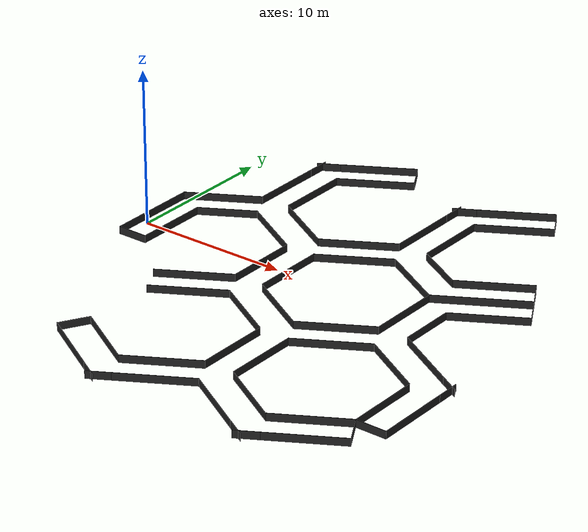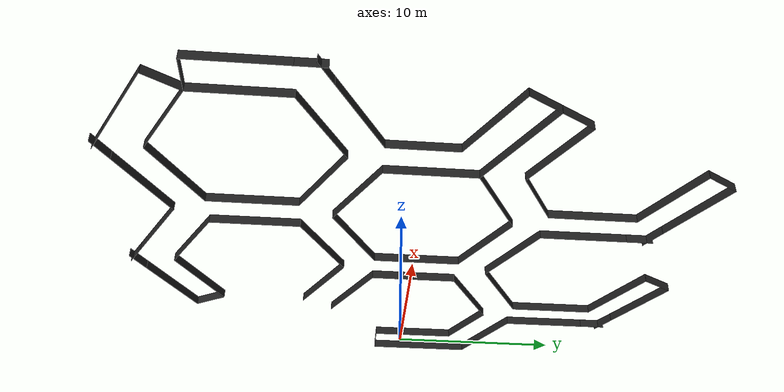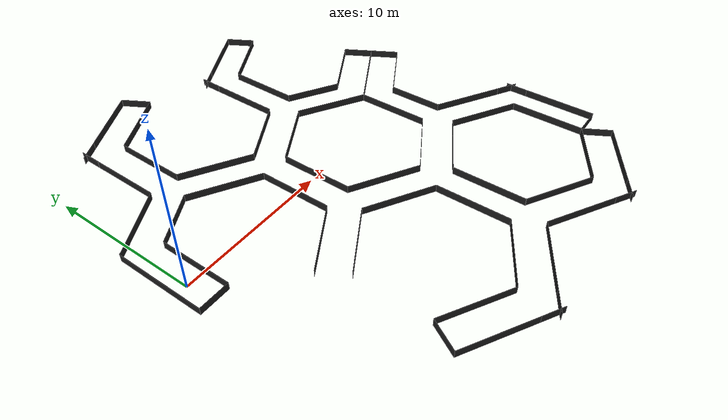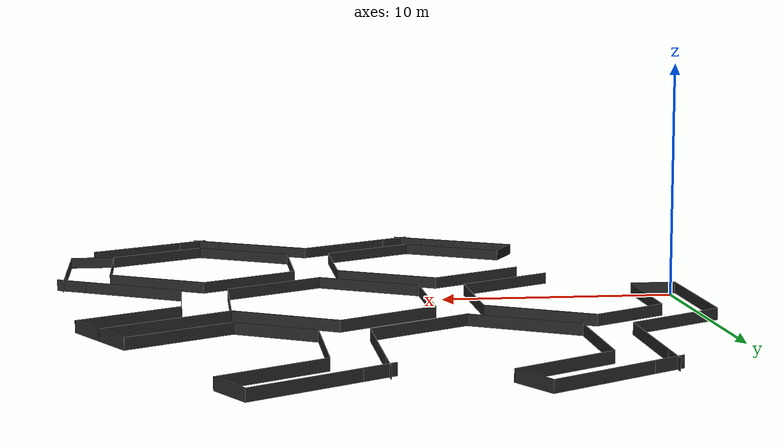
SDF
<?xml version='1.0'?>
<sdf version='1.6'>
  <model name='T_maze_right'>
    <link name='link'>
      <inertial>
        <mass>1</mass>
        <inertia>
          <ixx>0.166667</ixx>
          <ixy>0</ixy>
          <ixz>0</ixz>
          <iyy>0.166667</iyy>
          <iyz>0</iyz>
          <izz>0.166667</izz>
        </inertia>
        <pose frame=''>0 0 0 0 -0 0</pose>
      </inertial>
      <self_collide>0</self_collide>
      <enable_wind>0</enable_wind>
      <kinematic>0</kinematic>
      <pose frame=''>8.67982 0.164587 0 0 -0 0</pose>
      <gravity>1</gravity>
      <visual name='visual'>
        <geometry>
          <box>
            <size>0.015 4.8453 0.5</size>
          </box>
        </geometry>
        <material>
          <script>
            <name>Gazebo/FlatBlack</name>
            <uri>file://media/materials/scripts/gazebo.material</uri>
          </script>
          <shader type='pixel'>
            <normal_map>__default__</normal_map>
          </shader>
          <ambient>0.1 0.1 0.1 1</ambient>
          <diffuse>0.1 0.1 0.1 1</diffuse>
          <specular>0.01 0.01 0.01 1</specular>
          <emissive>0 0 0 1</emissive>
        </material>
        <pose frame=''>0 0 0 0 -0 0</pose>
        <transparency>0</transparency>
        <cast_shadows>1</cast_shadows>
      </visual>
      <visual name='ModelPreview_1::link::visual_2'>
        <geometry>
          <box>
            <size>0.015 4.8453 0.5</size>
          </box>
        </geometry>
        <material>
          <script>
            <name>Gazebo/FlatBlack</name>
            <uri>file://media/materials/scripts/gazebo.material</uri>
          </script>
          <shader type='pixel'>
            <normal_map>__default__</normal_map>
          </shader>
          <ambient>0.1 0.1 0.1 1</ambient>
          <diffuse>0.1 0.1 0.1 1</diffuse>
          <specular>0.01 0.01 0.01 1</specular>
          <emissive>0 0 0 1</emissive>
        </material>
        <pose frame=''>2 0 0 0 -0 0</pose>
        <transparency>0</transparency>
        <cast_shadows>1</cast_shadows>
      </visual>
      <collision name='collision_1'>
        <laser_retro>0</laser_retro>
        <max_contacts>10</max_contacts>
        <pose frame=''>2 0 0 0 -0 0</pose>
        <geometry>
          <box>
            <size>0.015 4.8453 0.5</size>
          </box>
        </geometry>
        <surface>
          <friction>
            <ode>
              <mu>1</mu>
              <mu2>1</mu2>
              <fdir1>0 0 0</fdir1>
              <slip1>0</slip1>
              <slip2>0</slip2>
            </ode>
            <torsional>
              <coefficient>1</coefficient>
              <patch_radius>0</patch_radius>
              <surface_radius>0</surface_radius>
              <use_patch_radius>1</use_patch_radius>
              <ode>
                <slip>0</slip>
              </ode>
            </torsional>
          </friction>
          <bounce>
            <restitution_coefficient>0</restitution_coefficient>
            <threshold>1e+06</threshold>
          </bounce>
          <contact>
            <collide_without_contact>0</collide_without_contact>
            <collide_without_contact_bitmask>1</collide_without_contact_bitmask>
            <collide_bitmask>1</collide_bitmask>
            <ode>
              <soft_cfm>0</soft_cfm>
              <soft_erp>0.2</soft_erp>
              <kp>1e+13</kp>
              <kd>1</kd>
              <max_vel>0.01</max_vel>
              <min_depth>0</min_depth>
            </ode>
            <bullet>
              <split_impulse>1</split_impulse>
              <split_impulse_penetration_threshold>-0.01</split_impulse_penetration_threshold>
              <soft_cfm>0</soft_cfm>
              <soft_erp>0.2</soft_erp>
              <kp>1e+13</kp>
              <kd>1</kd>
            </bullet>
          </contact>
        </surface>
      </collision>
      <collision name='collision'>
        <laser_retro>0</laser_retro>
        <max_contacts>10</max_contacts>
        <pose frame=''>0 0 0 0 -0 0</pose>
        <geometry>
          <box>
            <size>0.015 4.8453 0.5</size>
          </box>
        </geometry>
        <surface>
          <friction>
            <ode>
              <mu>1</mu>
              <mu2>1</mu2>
              <fdir1>0 0 0</fdir1>
              <slip1>0</slip1>
              <slip2>0</slip2>
            </ode>
            <torsional>
              <coefficient>1</coefficient>
              <patch_radius>0</patch_radius>
              <surface_radius>0</surface_radius>
              <use_patch_radius>1</use_patch_radius>
              <ode>
                <slip>0</slip>
              </ode>
            </torsional>
          </friction>
          <bounce>
            <restitution_coefficient>0</restitution_coefficient>
            <threshold>1e+06</threshold>
          </bounce>
          <contact>
            <collide_without_contact>0</collide_without_contact>
            <collide_without_contact_bitmask>1</collide_without_contact_bitmask>
            <collide_bitmask>1</collide_bitmask>
            <ode>
              <soft_cfm>0</soft_cfm>
              <soft_erp>0.2</soft_erp>
              <kp>1e+13</kp>
              <kd>1</kd>
              <max_vel>0.01</max_vel>
              <min_depth>0</min_depth>
            </ode>
            <bullet>
              <split_impulse>1</split_impulse>
              <split_impulse_penetration_threshold>-0.01</split_impulse_penetration_threshold>
              <soft_cfm>0</soft_cfm>
              <soft_erp>0.2</soft_erp>
              <kp>1e+13</kp>
              <kd>1</kd>
            </bullet>
          </contact>
        </surface>
      </collision>
    </link>
    <link name='link_clone'>
      <inertial>
        <mass>1</mass>
        <inertia>
          <ixx>0.166667</ixx>
          <ixy>0</ixy>
          <ixz>0</ixz>
          <iyy>0.166667</iyy>
          <iyz>0</iyz>
          <izz>0.166667</izz>
        </inertia>
        <pose frame=''>0 0 0 0 -0 0</pose>
      </inertial>
      <self_collide>0</self_collide>
      <enable_wind>0</enable_wind>
      <kinematic>0</kinematic>
      <pose frame=''>12.7749 3.79089 0 5e-06 -0 2.0944</pose>
      <gravity>1</gravity>
      <visual name='visual_2'>
        <geometry>
          <box>
            <size>0.015 4.8453 0.5</size>
          </box>
        </geometry>
        <material>
          <script>
            <name>Gazebo/FlatBlack</name>
            <uri>file://media/materials/scripts/gazebo.material</uri>
          </script>
          <shader type='pixel'>
            <normal_map>__default__</normal_map>
          </shader>
          <ambient>0.1 0.1 0.1 1</ambient>
          <diffuse>0.1 0.1 0.1 1</diffuse>
          <specular>0.01 0.01 0.01 1</specular>
          <emissive>0 0 0 1</emissive>
        </material>
        <pose frame=''>2 0 0 0 -0 0</pose>
        <transparency>0</transparency>
        <cast_shadows>1</cast_shadows>
      </visual>
      <visual name='visual'>
        <geometry>
          <box>
            <size>0.015 4.8453 0.5</size>
          </box>
        </geometry>
        <material>
          <script>
            <name>Gazebo/FlatBlack</name>
            <uri>file://media/materials/scripts/gazebo.material</uri>
          </script>
          <shader type='pixel'>
            <normal_map>__default__</normal_map>
          </shader>
          <ambient>0.1 0.1 0.1 1</ambient>
          <diffuse>0.1 0.1 0.1 1</diffuse>
          <specular>0.01 0.01 0.01 1</specular>
          <emissive>0 0 0 1</emissive>
        </material>
        <pose frame=''>0 0 0 0 -0 0</pose>
        <transparency>0</transparency>
        <cast_shadows>1</cast_shadows>
      </visual>
      <collision name='collision'>
        <laser_retro>0</laser_retro>
        <max_contacts>10</max_contacts>
        <pose frame=''>0 0 0 0 -0 0</pose>
        <geometry>
          <box>
            <size>0.015 4.8453 0.5</size>
          </box>
        </geometry>
        <surface>
          <friction>
            <ode>
              <mu>1</mu>
              <mu2>1</mu2>
              <fdir1>0 0 0</fdir1>
              <slip1>0</slip1>
              <slip2>0</slip2>
            </ode>
            <torsional>
              <coefficient>1</coefficient>
              <patch_radius>0</patch_radius>
              <surface_radius>0</surface_radius>
              <use_patch_radius>1</use_patch_radius>
              <ode>
                <slip>0</slip>
              </ode>
            </torsional>
          </friction>
          <bounce>
            <restitution_coefficient>0</restitution_coefficient>
            <threshold>1e+06</threshold>
          </bounce>
          <contact>
            <collide_without_contact>0</collide_without_contact>
            <collide_without_contact_bitmask>1</collide_without_contact_bitmask>
            <collide_bitmask>1</collide_bitmask>
            <ode>
              <soft_cfm>0</soft_cfm>
              <soft_erp>0.2</soft_erp>
              <kp>1e+13</kp>
              <kd>1</kd>
              <max_vel>0.01</max_vel>
              <min_depth>0</min_depth>
            </ode>
            <bullet>
              <split_impulse>1</split_impulse>
              <split_impulse_penetration_threshold>-0.01</split_impulse_penetration_threshold>
              <soft_cfm>0</soft_cfm>
              <soft_erp>0.2</soft_erp>
              <kp>1e+13</kp>
              <kd>1</kd>
            </bullet>
          </contact>
        </surface>
      </collision>
      <collision name='collision_1'>
        <laser_retro>0</laser_retro>
        <max_contacts>10</max_contacts>
        <pose frame=''>2 0 0 0 -0 0</pose>
        <geometry>
          <box>
            <size>0.015 4.8453 0.5</size>
          </box>
        </geometry>
        <surface>
          <friction>
            <ode>
              <mu>1</mu>
              <mu2>1</mu2>
              <fdir1>0 0 0</fdir1>
              <slip1>0</slip1>
              <slip2>0</slip2>
            </ode>
            <torsional>
              <coefficient>1</coefficient>
              <patch_radius>0</patch_radius>
              <surface_radius>0</surface_radius>
              <use_patch_radius>1</use_patch_radius>
              <ode>
                <slip>0</slip>
              </ode>
            </torsional>
          </friction>
          <bounce>
            <restitution_coefficient>0</restitution_coefficient>
            <threshold>1e+06</threshold>
          </bounce>
          <contact>
            <collide_without_contact>0</collide_without_contact>
            <collide_without_contact_bitmask>1</collide_without_contact_bitmask>
            <collide_bitmask>1</collide_bitmask>
            <ode>
              <soft_cfm>0</soft_cfm>
              <soft_erp>0.2</soft_erp>
              <kp>1e+13</kp>
              <kd>1</kd>
              <max_vel>0.01</max_vel>
              <min_depth>0</min_depth>
            </ode>
            <bullet>
              <split_impulse>1</split_impulse>
              <split_impulse_penetration_threshold>-0.01</split_impulse_penetration_threshold>
              <soft_cfm>0</soft_cfm>
              <soft_erp>0.2</soft_erp>
              <kp>1e+13</kp>
              <kd>1</kd>
            </bullet>
          </contact>
        </surface>
      </collision>
    </link>
    <link name='link_clone_0'>
      <inertial>
        <mass>1</mass>
        <inertia>
          <ixx>0.166667</ixx>
          <ixy>0</ixy>
          <ixz>0</ixz>
          <iyy>0.166667</iyy>
          <iyz>0</iyz>
          <izz>0.166667</izz>
        </inertia>
        <pose frame=''>0 0 0 0 -0 0</pose>
      </inertial>
      <self_collide>0</self_collide>
      <enable_wind>0</enable_wind>
      <kinematic>0</kinematic>
      <pose frame=''>7.58433 5.52401 0 5e-06 -0 -2.0944</pose>
      <gravity>1</gravity>
      <visual name='visual'>
        <geometry>
          <box>
            <size>0.015 4.8453 0.5</size>
          </box>
        </geometry>
        <material>
          <script>
            <name>Gazebo/FlatBlack</name>
            <uri>file://media/materials/scripts/gazebo.material</uri>
          </script>
          <shader type='pixel'>
            <normal_map>__default__</normal_map>
          </shader>
          <ambient>0.1 0.1 0.1 1</ambient>
          <diffuse>0.1 0.1 0.1 1</diffuse>
          <specular>0.01 0.01 0.01 1</specular>
          <emissive>0 0 0 1</emissive>
        </material>
        <pose frame=''>0 0 0 0 -0 0</pose>
        <transparency>0</transparency>
        <cast_shadows>1</cast_shadows>
      </visual>
      <visual name='visual_2'>
        <geometry>
          <box>
            <size>0.015 4.8453 0.5</size>
          </box>
        </geometry>
        <material>
          <script>
            <name>Gazebo/FlatBlack</name>
            <uri>file://media/materials/scripts/gazebo.material</uri>
          </script>
          <shader type='pixel'>
            <normal_map>__default__</normal_map>
          </shader>
          <ambient>0.1 0.1 0.1 1</ambient>
          <diffuse>0.1 0.1 0.1 1</diffuse>
          <specular>0.01 0.01 0.01 1</specular>
          <emissive>0 0 0 1</emissive>
        </material>
        <pose frame=''>2 0 0 0 -0 0</pose>
        <transparency>0</transparency>
        <cast_shadows>1</cast_shadows>
      </visual>
      <collision name='collision'>
        <laser_retro>0</laser_retro>
        <max_contacts>10</max_contacts>
        <pose frame=''>0 0 0 0 -0 0</pose>
        <geometry>
          <box>
            <size>0.015 4.8453 0.5</size>
          </box>
        </geometry>
        <surface>
          <friction>
            <ode>
              <mu>1</mu>
              <mu2>1</mu2>
              <fdir1>0 0 0</fdir1>
              <slip1>0</slip1>
              <slip2>0</slip2>
            </ode>
            <torsional>
              <coefficient>1</coefficient>
              <patch_radius>0</patch_radius>
              <surface_radius>0</surface_radius>
              <use_patch_radius>1</use_patch_radius>
              <ode>
                <slip>0</slip>
              </ode>
            </torsional>
          </friction>
          <bounce>
            <restitution_coefficient>0</restitution_coefficient>
            <threshold>1e+06</threshold>
          </bounce>
          <contact>
            <collide_without_contact>0</collide_without_contact>
            <collide_without_contact_bitmask>1</collide_without_contact_bitmask>
            <collide_bitmask>1</collide_bitmask>
            <ode>
              <soft_cfm>0</soft_cfm>
              <soft_erp>0.2</soft_erp>
              <kp>1e+13</kp>
              <kd>1</kd>
              <max_vel>0.01</max_vel>
              <min_depth>0</min_depth>
            </ode>
            <bullet>
              <split_impulse>1</split_impulse>
              <split_impulse_penetration_threshold>-0.01</split_impulse_penetration_threshold>
              <soft_cfm>0</soft_cfm>
              <soft_erp>0.2</soft_erp>
              <kp>1e+13</kp>
              <kd>1</kd>
            </bullet>
          </contact>
        </surface>
      </collision>
      <collision name='collision_1'>
        <laser_retro>0</laser_retro>
        <max_contacts>10</max_contacts>
        <pose frame=''>2 0 0 0 -0 0</pose>
        <geometry>
          <box>
            <size>0.015 4.8453 0.5</size>
          </box>
        </geometry>
        <surface>
          <friction>
            <ode>
              <mu>1</mu>
              <mu2>1</mu2>
              <fdir1>0 0 0</fdir1>
              <slip1>0</slip1>
              <slip2>0</slip2>
            </ode>
            <torsional>
              <coefficient>1</coefficient>
              <patch_radius>0</patch_radius>
              <surface_radius>0</surface_radius>
              <use_patch_radius>1</use_patch_radius>
              <ode>
                <slip>0</slip>
              </ode>
            </torsional>
          </friction>
          <bounce>
            <restitution_coefficient>0</restitution_coefficient>
            <threshold>1e+06</threshold>
          </bounce>
          <contact>
            <collide_without_contact>0</collide_without_contact>
            <collide_without_contact_bitmask>1</collide_without_contact_bitmask>
            <collide_bitmask>1</collide_bitmask>
            <ode>
              <soft_cfm>0</soft_cfm>
              <soft_erp>0.2</soft_erp>
              <kp>1e+13</kp>
              <kd>1</kd>
              <max_vel>0.01</max_vel>
              <min_depth>0</min_depth>
            </ode>
            <bullet>
              <split_impulse>1</split_impulse>
              <split_impulse_penetration_threshold>-0.01</split_impulse_penetration_threshold>
              <soft_cfm>0</soft_cfm>
              <soft_erp>0.2</soft_erp>
              <kp>1e+13</kp>
              <kd>1</kd>
            </bullet>
          </contact>
        </surface>
      </collision>
    </link>
    <link name='link_clone_0_clone'>
      <inertial>
        <mass>1</mass>
        <inertia>
          <ixx>0.166667</ixx>
          <ixy>0</ixy>
          <ixz>0</ixz>
          <iyy>0.166667</iyy>
          <iyz>0</iyz>
          <izz>0.166667</izz>
        </inertia>
        <pose frame=''>0 0 0 0 -0 0</pose>
      </inertial>
      <self_collide>0</self_collide>
      <enable_wind>0</enable_wind>
      <kinematic>0</kinematic>
      <pose frame=''>12.7746 -3.46264 0 5e-06 -0 -2.0944</pose>
      <gravity>1</gravity>
      <visual name='visual'>
        <geometry>
          <box>
            <size>0.015 4.8453 0.5</size>
          </box>
        </geometry>
        <material>
          <script>
            <name>Gazebo/FlatBlack</name>
            <uri>file://media/materials/scripts/gazebo.material</uri>
          </script>
          <shader type='pixel'>
            <normal_map>__default__</normal_map>
          </shader>
          <ambient>0.1 0.1 0.1 1</ambient>
          <diffuse>0.1 0.1 0.1 1</diffuse>
          <specular>0.01 0.01 0.01 1</specular>
          <emissive>0 0 0 1</emissive>
        </material>
        <pose frame=''>0 0 0 0 -0 0</pose>
        <transparency>0</transparency>
        <cast_shadows>1</cast_shadows>
      </visual>
      <visual name='visual_2'>
        <geometry>
          <box>
            <size>0.015 4.8453 0.5</size>
          </box>
        </geometry>
        <material>
          <script>
            <name>Gazebo/FlatBlack</name>
            <uri>file://media/materials/scripts/gazebo.material</uri>
          </script>
          <shader type='pixel'>
            <normal_map>__default__</normal_map>
          </shader>
          <ambient>0.1 0.1 0.1 1</ambient>
          <diffuse>0.1 0.1 0.1 1</diffuse>
          <specular>0.01 0.01 0.01 1</specular>
          <emissive>0 0 0 1</emissive>
        </material>
        <pose frame=''>2 0 0 0 -0 0</pose>
        <transparency>0</transparency>
        <cast_shadows>1</cast_shadows>
      </visual>
      <collision name='collision'>
        <laser_retro>0</laser_retro>
        <max_contacts>10</max_contacts>
        <pose frame=''>0 0 0 0 -0 0</pose>
        <geometry>
          <box>
            <size>0.015 4.8453 0.5</size>
          </box>
        </geometry>
        <surface>
          <friction>
            <ode>
              <mu>1</mu>
              <mu2>1</mu2>
              <fdir1>0 0 0</fdir1>
              <slip1>0</slip1>
              <slip2>0</slip2>
            </ode>
            <torsional>
              <coefficient>1</coefficient>
              <patch_radius>0</patch_radius>
              <surface_radius>0</surface_radius>
              <use_patch_radius>1</use_patch_radius>
              <ode>
                <slip>0</slip>
              </ode>
            </torsional>
          </friction>
          <bounce>
            <restitution_coefficient>0</restitution_coefficient>
            <threshold>1e+06</threshold>
          </bounce>
          <contact>
            <collide_without_contact>0</collide_without_contact>
            <collide_without_contact_bitmask>1</collide_without_contact_bitmask>
            <collide_bitmask>1</collide_bitmask>
            <ode>
              <soft_cfm>0</soft_cfm>
              <soft_erp>0.2</soft_erp>
              <kp>1e+13</kp>
              <kd>1</kd>
              <max_vel>0.01</max_vel>
              <min_depth>0</min_depth>
            </ode>
            <bullet>
              <split_impulse>1</split_impulse>
              <split_impulse_penetration_threshold>-0.01</split_impulse_penetration_threshold>
              <soft_cfm>0</soft_cfm>
              <soft_erp>0.2</soft_erp>
              <kp>1e+13</kp>
              <kd>1</kd>
            </bullet>
          </contact>
        </surface>
      </collision>
      <collision name='collision_1'>
        <laser_retro>0</laser_retro>
        <max_contacts>10</max_contacts>
        <pose frame=''>2 0 0 0 -0 0</pose>
        <geometry>
          <box>
            <size>0.015 4.8453 0.5</size>
          </box>
        </geometry>
        <surface>
          <friction>
            <ode>
              <mu>1</mu>
              <mu2>1</mu2>
              <fdir1>0 0 0</fdir1>
              <slip1>0</slip1>
              <slip2>0</slip2>
            </ode>
            <torsional>
              <coefficient>1</coefficient>
              <patch_radius>0</patch_radius>
              <surface_radius>0</surface_radius>
              <use_patch_radius>1</use_patch_radius>
              <ode>
                <slip>0</slip>
              </ode>
            </torsional>
          </friction>
          <bounce>
            <restitution_coefficient>0</restitution_coefficient>
            <threshold>1e+06</threshold>
          </bounce>
          <contact>
            <collide_without_contact>0</collide_without_contact>
            <collide_without_contact_bitmask>1</collide_without_contact_bitmask>
            <collide_bitmask>1</collide_bitmask>
            <ode>
              <soft_cfm>0</soft_cfm>
              <soft_erp>0.2</soft_erp>
              <kp>1e+13</kp>
              <kd>1</kd>
              <max_vel>0.01</max_vel>
              <min_depth>0</min_depth>
            </ode>
            <bullet>
              <split_impulse>1</split_impulse>
              <split_impulse_penetration_threshold>-0.01</split_impulse_penetration_threshold>
              <soft_cfm>0</soft_cfm>
              <soft_erp>0.2</soft_erp>
              <kp>1e+13</kp>
              <kd>1</kd>
            </bullet>
          </contact>
        </surface>
      </collision>
    </link>
    <link name='link_clone_0_clone_clone'>
      <inertial>
        <mass>1</mass>
        <inertia>
          <ixx>0.166667</ixx>
          <ixy>0</ixy>
          <ixz>0</ixz>
          <iyy>0.166667</iyy>
          <iyz>0</iyz>
          <izz>0.166667</izz>
        </inertia>
        <pose frame=''>0 0 0 0 -0 0</pose>
      </inertial>
      <self_collide>0</self_collide>
      <enable_wind>0</enable_wind>
      <kinematic>0</kinematic>
      <pose frame=''>17.958 -12.4374 0 5e-06 -0 -2.0944</pose>
      <gravity>1</gravity>
      <visual name='visual'>
        <geometry>
          <box>
            <size>0.015 4.8453 0.5</size>
          </box>
        </geometry>
        <material>
          <script>
            <name>Gazebo/FlatBlack</name>
            <uri>file://media/materials/scripts/gazebo.material</uri>
          </script>
          <shader type='pixel'>
            <normal_map>__default__</normal_map>
          </shader>
          <ambient>0.1 0.1 0.1 1</ambient>
          <diffuse>0.1 0.1 0.1 1</diffuse>
          <specular>0.01 0.01 0.01 1</specular>
          <emissive>0 0 0 1</emissive>
        </material>
        <pose frame=''>0 0 0 0 -0 0</pose>
        <transparency>0</transparency>
        <cast_shadows>1</cast_shadows>
      </visual>
      <visual name='visual_2'>
        <geometry>
          <box>
            <size>0.015 4.8453 0.5</size>
          </box>
        </geometry>
        <material>
          <script>
            <name>Gazebo/FlatBlack</name>
            <uri>file://media/materials/scripts/gazebo.material</uri>
          </script>
          <shader type='pixel'>
            <normal_map>__default__</normal_map>
          </shader>
          <ambient>0.1 0.1 0.1 1</ambient>
          <diffuse>0.1 0.1 0.1 1</diffuse>
          <specular>0.01 0.01 0.01 1</specular>
          <emissive>0 0 0 1</emissive>
        </material>
        <pose frame=''>2 0 0 0 -0 0</pose>
        <transparency>0</transparency>
        <cast_shadows>1</cast_shadows>
      </visual>
      <collision name='collision'>
        <laser_retro>0</laser_retro>
        <max_contacts>10</max_contacts>
        <pose frame=''>0 0 0 0 -0 0</pose>
        <geometry>
          <box>
            <size>0.015 4.8453 0.5</size>
          </box>
        </geometry>
        <surface>
          <friction>
            <ode>
              <mu>1</mu>
              <mu2>1</mu2>
              <fdir1>0 0 0</fdir1>
              <slip1>0</slip1>
              <slip2>0</slip2>
            </ode>
            <torsional>
              <coefficient>1</coefficient>
              <patch_radius>0</patch_radius>
              <surface_radius>0</surface_radius>
              <use_patch_radius>1</use_patch_radius>
              <ode>
                <slip>0</slip>
              </ode>
            </torsional>
          </friction>
          <bounce>
            <restitution_coefficient>0</restitution_coefficient>
            <threshold>1e+06</threshold>
          </bounce>
          <contact>
            <collide_without_contact>0</collide_without_contact>
            <collide_without_contact_bitmask>1</collide_without_contact_bitmask>
            <collide_bitmask>1</collide_bitmask>
            <ode>
              <soft_cfm>0</soft_cfm>
              <soft_erp>0.2</soft_erp>
              <kp>1e+13</kp>
              <kd>1</kd>
              <max_vel>0.01</max_vel>
              <min_depth>0</min_depth>
            </ode>
            <bullet>
              <split_impulse>1</split_impulse>
              <split_impulse_penetration_threshold>-0.01</split_impulse_penetration_threshold>
              <soft_cfm>0</soft_cfm>
              <soft_erp>0.2</soft_erp>
              <kp>1e+13</kp>
              <kd>1</kd>
            </bullet>
          </contact>
        </surface>
      </collision>
      <collision name='collision_1'>
        <laser_retro>0</laser_retro>
        <max_contacts>10</max_contacts>
        <pose frame=''>2 0 0 0 -0 0</pose>
        <geometry>
          <box>
            <size>0.015 4.8453 0.5</size>
          </box>
        </geometry>
        <surface>
          <friction>
            <ode>
              <mu>1</mu>
              <mu2>1</mu2>
              <fdir1>0 0 0</fdir1>
              <slip1>0</slip1>
              <slip2>0</slip2>
            </ode>
            <torsional>
              <coefficient>1</coefficient>
              <patch_radius>0</patch_radius>
              <surface_radius>0</surface_radius>
              <use_patch_radius>1</use_patch_radius>
              <ode>
                <slip>0</slip>
              </ode>
            </torsional>
          </friction>
          <bounce>
            <restitution_coefficient>0</restitution_coefficient>
            <threshold>1e+06</threshold>
          </bounce>
          <contact>
            <collide_without_contact>0</collide_without_contact>
            <collide_without_contact_bitmask>1</collide_without_contact_bitmask>
            <collide_bitmask>1</collide_bitmask>
            <ode>
              <soft_cfm>0</soft_cfm>
              <soft_erp>0.2</soft_erp>
              <kp>1e+13</kp>
              <kd>1</kd>
              <max_vel>0.01</max_vel>
              <min_depth>0</min_depth>
            </ode>
            <bullet>
              <split_impulse>1</split_impulse>
              <split_impulse_penetration_threshold>-0.01</split_impulse_penetration_threshold>
              <soft_cfm>0</soft_cfm>
              <soft_erp>0.2</soft_erp>
              <kp>1e+13</kp>
              <kd>1</kd>
            </bullet>
          </contact>
        </surface>
      </collision>
    </link>
    <link name='link_clone_0_clone_clone_0'>
      <inertial>
        <mass>1</mass>
        <inertia>
          <ixx>0.166667</ixx>
          <ixy>0</ixy>
          <ixz>0</ixz>
          <iyy>0.166667</iyy>
          <iyz>0</iyz>
          <izz>0.166667</izz>
        </inertia>
        <pose frame=''>0 0 0 0 -0 0</pose>
      </inertial>
      <self_collide>0</self_collide>
      <enable_wind>0</enable_wind>
      <kinematic>0</kinematic>
      <pose frame=''>7.58617 -12.4482 0 5e-06 -0 -2.0944</pose>
      <gravity>1</gravity>
      <visual name='visual'>
        <geometry>
          <box>
            <size>0.015 4.8453 0.5</size>
          </box>
        </geometry>
        <material>
          <script>
            <name>Gazebo/FlatBlack</name>
            <uri>file://media/materials/scripts/gazebo.material</uri>
          </script>
          <shader type='pixel'>
            <normal_map>__default__</normal_map>
          </shader>
          <ambient>0.1 0.1 0.1 1</ambient>
          <diffuse>0.1 0.1 0.1 1</diffuse>
          <specular>0.01 0.01 0.01 1</specular>
          <emissive>0 0 0 1</emissive>
        </material>
        <pose frame=''>0 0 0 0 -0 0</pose>
        <transparency>0</transparency>
        <cast_shadows>1</cast_shadows>
      </visual>
      <visual name='visual_2'>
        <geometry>
          <box>
            <size>0.015 4.8453 0.5</size>
          </box>
        </geometry>
        <material>
          <script>
            <name>Gazebo/FlatBlack</name>
            <uri>file://media/materials/scripts/gazebo.material</uri>
          </script>
          <shader type='pixel'>
            <normal_map>__default__</normal_map>
          </shader>
          <ambient>0.1 0.1 0.1 1</ambient>
          <diffuse>0.1 0.1 0.1 1</diffuse>
          <specular>0.01 0.01 0.01 1</specular>
          <emissive>0 0 0 1</emissive>
        </material>
        <pose frame=''>2 0 0 0 -0 0</pose>
        <transparency>0</transparency>
        <cast_shadows>1</cast_shadows>
      </visual>
      <collision name='collision_1'>
        <laser_retro>0</laser_retro>
        <max_contacts>10</max_contacts>
        <pose frame=''>2 0 0 0 -0 0</pose>
        <geometry>
          <box>
            <size>0.015 4.8453 0.5</size>
          </box>
        </geometry>
        <surface>
          <friction>
            <ode>
              <mu>1</mu>
              <mu2>1</mu2>
              <fdir1>0 0 0</fdir1>
              <slip1>0</slip1>
              <slip2>0</slip2>
            </ode>
            <torsional>
              <coefficient>1</coefficient>
              <patch_radius>0</patch_radius>
              <surface_radius>0</surface_radius>
              <use_patch_radius>1</use_patch_radius>
              <ode>
                <slip>0</slip>
              </ode>
            </torsional>
          </friction>
          <bounce>
            <restitution_coefficient>0</restitution_coefficient>
            <threshold>1e+06</threshold>
          </bounce>
          <contact>
            <collide_without_contact>0</collide_without_contact>
            <collide_without_contact_bitmask>1</collide_without_contact_bitmask>
            <collide_bitmask>1</collide_bitmask>
            <ode>
              <soft_cfm>0</soft_cfm>
              <soft_erp>0.2</soft_erp>
              <kp>1e+13</kp>
              <kd>1</kd>
              <max_vel>0.01</max_vel>
              <min_depth>0</min_depth>
            </ode>
            <bullet>
              <split_impulse>1</split_impulse>
              <split_impulse_penetration_threshold>-0.01</split_impulse_penetration_threshold>
              <soft_cfm>0</soft_cfm>
              <soft_erp>0.2</soft_erp>
              <kp>1e+13</kp>
              <kd>1</kd>
            </bullet>
          </contact>
        </surface>
      </collision>
      <collision name='collision'>
        <laser_retro>0</laser_retro>
        <max_contacts>10</max_contacts>
        <pose frame=''>0 0 0 0 -0 0</pose>
        <geometry>
          <box>
            <size>0.015 4.8453 0.5</size>
          </box>
        </geometry>
        <surface>
          <friction>
            <ode>
              <mu>1</mu>
              <mu2>1</mu2>
              <fdir1>0 0 0</fdir1>
              <slip1>0</slip1>
              <slip2>0</slip2>
            </ode>
            <torsional>
              <coefficient>1</coefficient>
              <patch_radius>0</patch_radius>
              <surface_radius>0</surface_radius>
              <use_patch_radius>1</use_patch_radius>
              <ode>
                <slip>0</slip>
              </ode>
            </torsional>
          </friction>
          <bounce>
            <restitution_coefficient>0</restitution_coefficient>
            <threshold>1e+06</threshold>
          </bounce>
          <contact>
            <collide_without_contact>0</collide_without_contact>
            <collide_without_contact_bitmask>1</collide_without_contact_bitmask>
            <collide_bitmask>1</collide_bitmask>
            <ode>
              <soft_cfm>0</soft_cfm>
              <soft_erp>0.2</soft_erp>
              <kp>1e+13</kp>
              <kd>1</kd>
              <max_vel>0.01</max_vel>
              <min_depth>0</min_depth>
            </ode>
            <bullet>
              <split_impulse>1</split_impulse>
              <split_impulse_penetration_threshold>-0.01</split_impulse_penetration_threshold>
              <soft_cfm>0</soft_cfm>
              <soft_erp>0.2</soft_erp>
              <kp>1e+13</kp>
              <kd>1</kd>
            </bullet>
          </contact>
        </surface>
      </collision>
    </link>
    <link name='link_clone_0_clone_clone_1'>
      <inertial>
        <mass>1</mass>
        <inertia>
          <ixx>0.166667</ixx>
          <ixy>0</ixy>
          <ixz>0</ixz>
          <iyy>0.166667</iyy>
          <iyz>0</iyz>
          <izz>0.166667</izz>
        </inertia>
        <pose frame=''>0 0 0 0 -0 0</pose>
      </inertial>
      <self_collide>0</self_collide>
      <enable_wind>0</enable_wind>
      <kinematic>0</kinematic>
      <pose frame=''>17.9599 5.5227 1e-06 5e-06 -0 -2.0944</pose>
      <gravity>1</gravity>
      <visual name='visual_2'>
        <geometry>
          <box>
            <size>0.015 4.8453 0.5</size>
          </box>
        </geometry>
        <material>
          <script>
            <name>Gazebo/FlatBlack</name>
            <uri>file://media/materials/scripts/gazebo.material</uri>
          </script>
          <shader type='pixel'>
            <normal_map>__default__</normal_map>
          </shader>
          <ambient>0.1 0.1 0.1 1</ambient>
          <diffuse>0.1 0.1 0.1 1</diffuse>
          <specular>0.01 0.01 0.01 1</specular>
          <emissive>0 0 0 1</emissive>
        </material>
        <pose frame=''>2 0 0 0 -0 0</pose>
        <transparency>0</transparency>
        <cast_shadows>1</cast_shadows>
      </visual>
      <visual name='visual'>
        <geometry>
          <box>
            <size>0.015 3.7053 0.5</size>
          </box>
        </geometry>
        <material>
          <script>
            <name>Gazebo/FlatBlack</name>
            <uri>file://media/materials/scripts/gazebo.material</uri>
          </script>
          <shader type='pixel'>
            <normal_map>__default__</normal_map>
          </shader>
          <ambient>0.1 0.1 0.1 1</ambient>
          <diffuse>0.1 0.1 0.1 1</diffuse>
          <specular>0.01 0.01 0.01 1</specular>
          <emissive>0 0 0 1</emissive>
        </material>
        <pose frame=''>0 -0.57 0 0 -0 0</pose>
        <transparency>0</transparency>
        <cast_shadows>1</cast_shadows>
      </visual>
      <collision name='collision_1'>
        <laser_retro>0</laser_retro>
        <max_contacts>10</max_contacts>
        <pose frame=''>2 0 0 0 -0 0</pose>
        <geometry>
          <box>
            <size>0.015 4.8453 0.5</size>
          </box>
        </geometry>
        <surface>
          <friction>
            <ode>
              <mu>1</mu>
              <mu2>1</mu2>
              <fdir1>0 0 0</fdir1>
              <slip1>0</slip1>
              <slip2>0</slip2>
            </ode>
            <torsional>
              <coefficient>1</coefficient>
              <patch_radius>0</patch_radius>
              <surface_radius>0</surface_radius>
              <use_patch_radius>1</use_patch_radius>
              <ode>
                <slip>0</slip>
              </ode>
            </torsional>
          </friction>
          <bounce>
            <restitution_coefficient>0</restitution_coefficient>
            <threshold>1e+06</threshold>
          </bounce>
          <contact>
            <collide_without_contact>0</collide_without_contact>
            <collide_without_contact_bitmask>1</collide_without_contact_bitmask>
            <collide_bitmask>1</collide_bitmask>
            <ode>
              <soft_cfm>0</soft_cfm>
              <soft_erp>0.2</soft_erp>
              <kp>1e+13</kp>
              <kd>1</kd>
              <max_vel>0.01</max_vel>
              <min_depth>0</min_depth>
            </ode>
            <bullet>
              <split_impulse>1</split_impulse>
              <split_impulse_penetration_threshold>-0.01</split_impulse_penetration_threshold>
              <soft_cfm>0</soft_cfm>
              <soft_erp>0.2</soft_erp>
              <kp>1e+13</kp>
              <kd>1</kd>
            </bullet>
          </contact>
        </surface>
      </collision>
      <collision name='collision'>
        <laser_retro>0</laser_retro>
        <max_contacts>10</max_contacts>
        <pose frame=''>0 -0.57 0 0 -0 0</pose>
        <geometry>
          <box>
            <size>0.015 3.7053 0.5</size>
          </box>
        </geometry>
        <surface>
          <friction>
            <ode>
              <mu>1</mu>
              <mu2>1</mu2>
              <fdir1>0 0 0</fdir1>
              <slip1>0</slip1>
              <slip2>0</slip2>
            </ode>
            <torsional>
              <coefficient>1</coefficient>
              <patch_radius>0</patch_radius>
              <surface_radius>0</surface_radius>
              <use_patch_radius>1</use_patch_radius>
              <ode>
                <slip>0</slip>
              </ode>
            </torsional>
          </friction>
          <bounce>
            <restitution_coefficient>0</restitution_coefficient>
            <threshold>1e+06</threshold>
          </bounce>
          <contact>
            <collide_without_contact>0</collide_without_contact>
            <collide_without_contact_bitmask>1</collide_without_contact_bitmask>
            <collide_bitmask>1</collide_bitmask>
            <ode>
              <soft_cfm>0</soft_cfm>
              <soft_erp>0.2</soft_erp>
              <kp>1e+13</kp>
              <kd>1</kd>
              <max_vel>0.01</max_vel>
              <min_depth>0</min_depth>
            </ode>
            <bullet>
              <split_impulse>1</split_impulse>
              <split_impulse_penetration_threshold>-0.01</split_impulse_penetration_threshold>
              <soft_cfm>0</soft_cfm>
              <soft_erp>0.2</soft_erp>
              <kp>1e+13</kp>
              <kd>1</kd>
            </bullet>
          </contact>
        </surface>
      </collision>
    </link>
    <link name='link_clone_0_clone_clone_1_clone'>
      <inertial>
        <mass>1</mass>
        <inertia>
          <ixx>0.166667</ixx>
          <ixy>0</ixy>
          <ixz>0</ixz>
          <iyy>0.166667</iyy>
          <iyz>0</iyz>
          <izz>0.166667</izz>
        </inertia>
        <pose frame=''>0 0 0 0 -0 0</pose>
      </inertial>
      <self_collide>0</self_collide>
      <enable_wind>0</enable_wind>
      <kinematic>0</kinematic>
      <pose frame=''>19.0569 0.16687 -6e-06 5e-06 -0 0</pose>
      <gravity>1</gravity>
      <visual name='visual'>
        <geometry>
          <box>
            <size>0.015 4.8453 0.5</size>
          </box>
        </geometry>
        <material>
          <script>
            <name>Gazebo/FlatBlack</name>
            <uri>file://media/materials/scripts/gazebo.material</uri>
          </script>
          <shader type='pixel'>
            <normal_map>__default__</normal_map>
          </shader>
          <ambient>0.1 0.1 0.1 1</ambient>
          <diffuse>0.1 0.1 0.1 1</diffuse>
          <specular>0.01 0.01 0.01 1</specular>
          <emissive>0 0 0 1</emissive>
        </material>
        <pose frame=''>0 0 0 0 -0 0</pose>
        <transparency>0</transparency>
        <cast_shadows>1</cast_shadows>
      </visual>
      <visual name='visual_2'>
        <geometry>
          <box>
            <size>0.015 3.7053 0.5</size>
          </box>
        </geometry>
        <material>
          <script>
            <name>Gazebo/FlatBlack</name>
            <uri>file://media/materials/scripts/gazebo.material</uri>
          </script>
          <shader type='pixel'>
            <normal_map>__default__</normal_map>
          </shader>
          <ambient>0.1 0.1 0.1 1</ambient>
          <diffuse>0.1 0.1 0.1 1</diffuse>
          <specular>0.01 0.01 0.01 1</specular>
          <emissive>0 0 0 1</emissive>
        </material>
        <pose frame=''>2 -0.57 0 0 -0 0</pose>
        <transparency>0</transparency>
        <cast_shadows>1</cast_shadows>
      </visual>
      <collision name='collision_1'>
        <laser_retro>0</laser_retro>
        <max_contacts>10</max_contacts>
        <pose frame=''>2 -0.57 0 0 -0 0</pose>
        <geometry>
          <box>
            <size>0.015 3.7053 0.5</size>
          </box>
        </geometry>
        <surface>
          <friction>
            <ode>
              <mu>1</mu>
              <mu2>1</mu2>
              <fdir1>0 0 0</fdir1>
              <slip1>0</slip1>
              <slip2>0</slip2>
            </ode>
            <torsional>
              <coefficient>1</coefficient>
              <patch_radius>0</patch_radius>
              <surface_radius>0</surface_radius>
              <use_patch_radius>1</use_patch_radius>
              <ode>
                <slip>0</slip>
              </ode>
            </torsional>
          </friction>
          <bounce>
            <restitution_coefficient>0</restitution_coefficient>
            <threshold>1e+06</threshold>
          </bounce>
          <contact>
            <collide_without_contact>0</collide_without_contact>
            <collide_without_contact_bitmask>1</collide_without_contact_bitmask>
            <collide_bitmask>1</collide_bitmask>
            <ode>
              <soft_cfm>0</soft_cfm>
              <soft_erp>0.2</soft_erp>
              <kp>1e+13</kp>
              <kd>1</kd>
              <max_vel>0.01</max_vel>
              <min_depth>0</min_depth>
            </ode>
            <bullet>
              <split_impulse>1</split_impulse>
              <split_impulse_penetration_threshold>-0.01</split_impulse_penetration_threshold>
              <soft_cfm>0</soft_cfm>
              <soft_erp>0.2</soft_erp>
              <kp>1e+13</kp>
              <kd>1</kd>
            </bullet>
          </contact>
        </surface>
      </collision>
      <collision name='collision'>
        <laser_retro>0</laser_retro>
        <max_contacts>10</max_contacts>
        <pose frame=''>0 0 0 0 -0 0</pose>
        <geometry>
          <box>
            <size>0.015 4.8453 0.5</size>
          </box>
        </geometry>
        <surface>
          <friction>
            <ode>
              <mu>1</mu>
              <mu2>1</mu2>
              <fdir1>0 0 0</fdir1>
              <slip1>0</slip1>
              <slip2>0</slip2>
            </ode>
            <torsional>
              <coefficient>1</coefficient>
              <patch_radius>0</patch_radius>
              <surface_radius>0</surface_radius>
              <use_patch_radius>1</use_patch_radius>
              <ode>
                <slip>0</slip>
              </ode>
            </torsional>
          </friction>
          <bounce>
            <restitution_coefficient>0</restitution_coefficient>
            <threshold>1e+06</threshold>
          </bounce>
          <contact>
            <collide_without_contact>0</collide_without_contact>
            <collide_without_contact_bitmask>1</collide_without_contact_bitmask>
            <collide_bitmask>1</collide_bitmask>
            <ode>
              <soft_cfm>0</soft_cfm>
              <soft_erp>0.2</soft_erp>
              <kp>1e+13</kp>
              <kd>1</kd>
              <max_vel>0.01</max_vel>
              <min_depth>0</min_depth>
            </ode>
            <bullet>
              <split_impulse>1</split_impulse>
              <split_impulse_penetration_threshold>-0.01</split_impulse_penetration_threshold>
              <soft_cfm>0</soft_cfm>
              <soft_erp>0.2</soft_erp>
              <kp>1e+13</kp>
              <kd>1</kd>
            </bullet>
          </contact>
        </surface>
      </collision>
    </link>
    <link name='link_clone_0_clone_clone_1_clone_0'>
      <inertial>
        <mass>1</mass>
        <inertia>
          <ixx>0.166667</ixx>
          <ixy>0</ixy>
          <ixz>0</ixz>
          <iyy>0.166667</iyy>
          <iyz>0</iyz>
          <izz>0.166667</izz>
        </inertia>
        <pose frame=''>0 0 0 0 -0 0</pose>
      </inertial>
      <self_collide>0</self_collide>
      <enable_wind>0</enable_wind>
      <kinematic>0</kinematic>
      <pose frame=''>2.39592 3.79036 1e-06 5e-06 -0 2.0944</pose>
      <gravity>1</gravity>
      <visual name='visual'>
        <geometry>
          <box>
            <size>0.015 3.7053 0.5</size>
          </box>
        </geometry>
        <material>
          <script>
            <name>Gazebo/FlatBlack</name>
            <uri>file://media/materials/scripts/gazebo.material</uri>
          </script>
          <shader type='pixel'>
            <normal_map>__default__</normal_map>
          </shader>
          <ambient>0.1 0.1 0.1 1</ambient>
          <diffuse>0.1 0.1 0.1 1</diffuse>
          <specular>0.01 0.01 0.01 1</specular>
          <emissive>0 0 0 1</emissive>
        </material>
        <pose frame=''>0 -0.57 0 0 -0 0</pose>
        <transparency>0</transparency>
        <cast_shadows>1</cast_shadows>
      </visual>
      <visual name='visual_2'>
        <geometry>
          <box>
            <size>0.015 4.8453 0.5</size>
          </box>
        </geometry>
        <material>
          <script>
            <name>Gazebo/FlatBlack</name>
            <uri>file://media/materials/scripts/gazebo.material</uri>
          </script>
          <shader type='pixel'>
            <normal_map>__default__</normal_map>
          </shader>
          <ambient>0.1 0.1 0.1 1</ambient>
          <diffuse>0.1 0.1 0.1 1</diffuse>
          <specular>0.01 0.01 0.01 1</specular>
          <emissive>0 0 0 1</emissive>
        </material>
        <pose frame=''>2 0 0 0 -0 0</pose>
        <transparency>0</transparency>
        <cast_shadows>1</cast_shadows>
      </visual>
      <collision name='collision'>
        <laser_retro>0</laser_retro>
        <max_contacts>10</max_contacts>
        <pose frame=''>0 -0.57 0 0 -0 0</pose>
        <geometry>
          <box>
            <size>0.015 3.7053 0.5</size>
          </box>
        </geometry>
        <surface>
          <friction>
            <ode>
              <mu>1</mu>
              <mu2>1</mu2>
              <fdir1>0 0 0</fdir1>
              <slip1>0</slip1>
              <slip2>0</slip2>
            </ode>
            <torsional>
              <coefficient>1</coefficient>
              <patch_radius>0</patch_radius>
              <surface_radius>0</surface_radius>
              <use_patch_radius>1</use_patch_radius>
              <ode>
                <slip>0</slip>
              </ode>
            </torsional>
          </friction>
          <bounce>
            <restitution_coefficient>0</restitution_coefficient>
            <threshold>1e+06</threshold>
          </bounce>
          <contact>
            <collide_without_contact>0</collide_without_contact>
            <collide_without_contact_bitmask>1</collide_without_contact_bitmask>
            <collide_bitmask>1</collide_bitmask>
            <ode>
              <soft_cfm>0</soft_cfm>
              <soft_erp>0.2</soft_erp>
              <kp>1e+13</kp>
              <kd>1</kd>
              <max_vel>0.01</max_vel>
              <min_depth>0</min_depth>
            </ode>
            <bullet>
              <split_impulse>1</split_impulse>
              <split_impulse_penetration_threshold>-0.01</split_impulse_penetration_threshold>
              <soft_cfm>0</soft_cfm>
              <soft_erp>0.2</soft_erp>
              <kp>1e+13</kp>
              <kd>1</kd>
            </bullet>
          </contact>
        </surface>
      </collision>
      <collision name='collision_1'>
        <laser_retro>0</laser_retro>
        <max_contacts>10</max_contacts>
        <pose frame=''>2 0 0 0 -0 0</pose>
        <geometry>
          <box>
            <size>0.015 4.8453 0.5</size>
          </box>
        </geometry>
        <surface>
          <friction>
            <ode>
              <mu>1</mu>
              <mu2>1</mu2>
              <fdir1>0 0 0</fdir1>
              <slip1>0</slip1>
              <slip2>0</slip2>
            </ode>
            <torsional>
              <coefficient>1</coefficient>
              <patch_radius>0</patch_radius>
              <surface_radius>0</surface_radius>
              <use_patch_radius>1</use_patch_radius>
              <ode>
                <slip>0</slip>
              </ode>
            </torsional>
          </friction>
          <bounce>
            <restitution_coefficient>0</restitution_coefficient>
            <threshold>1e+06</threshold>
          </bounce>
          <contact>
            <collide_without_contact>0</collide_without_contact>
            <collide_without_contact_bitmask>1</collide_without_contact_bitmask>
            <collide_bitmask>1</collide_bitmask>
            <ode>
              <soft_cfm>0</soft_cfm>
              <soft_erp>0.2</soft_erp>
              <kp>1e+13</kp>
              <kd>1</kd>
              <max_vel>0.01</max_vel>
              <min_depth>0</min_depth>
            </ode>
            <bullet>
              <split_impulse>1</split_impulse>
              <split_impulse_penetration_threshold>-0.01</split_impulse_penetration_threshold>
              <soft_cfm>0</soft_cfm>
              <soft_erp>0.2</soft_erp>
              <kp>1e+13</kp>
              <kd>1</kd>
            </bullet>
          </contact>
        </surface>
      </collision>
    </link>
    <link name='link_clone_0_clone_clone_clone'>
      <inertial>
        <mass>1</mass>
        <inertia>
          <ixx>0.166667</ixx>
          <ixy>0</ixy>
          <ixz>0</ixz>
          <iyy>0.166667</iyy>
          <iyz>0</iyz>
          <izz>0.166667</izz>
        </inertia>
        <pose frame=''>0 0 0 0 -0 0</pose>
      </inertial>
      <self_collide>0</self_collide>
      <enable_wind>0</enable_wind>
      <kinematic>0</kinematic>
      <pose frame=''>23.1519 -3.46238 0 5e-06 -0 -2.0944</pose>
      <gravity>1</gravity>
      <visual name='visual'>
        <geometry>
          <box>
            <size>0.015 4.8453 0.5</size>
          </box>
        </geometry>
        <material>
          <script>
            <name>Gazebo/FlatBlack</name>
            <uri>file://media/materials/scripts/gazebo.material</uri>
          </script>
          <shader type='pixel'>
            <normal_map>__default__</normal_map>
          </shader>
          <ambient>0.1 0.1 0.1 1</ambient>
          <diffuse>0.1 0.1 0.1 1</diffuse>
          <specular>0.01 0.01 0.01 1</specular>
          <emissive>0 0 0 1</emissive>
        </material>
        <pose frame=''>0 0 0 0 -0 0</pose>
        <transparency>0</transparency>
        <cast_shadows>1</cast_shadows>
      </visual>
      <visual name='visual_2'>
        <geometry>
          <box>
            <size>0.015 4.8453 0.5</size>
          </box>
        </geometry>
        <material>
          <script>
            <name>Gazebo/FlatBlack</name>
            <uri>file://media/materials/scripts/gazebo.material</uri>
          </script>
          <shader type='pixel'>
            <normal_map>__default__</normal_map>
          </shader>
          <ambient>0.1 0.1 0.1 1</ambient>
          <diffuse>0.1 0.1 0.1 1</diffuse>
          <specular>0.01 0.01 0.01 1</specular>
          <emissive>0 0 0 1</emissive>
        </material>
        <pose frame=''>2 0 0 0 -0 0</pose>
        <transparency>0</transparency>
        <cast_shadows>1</cast_shadows>
      </visual>
      <collision name='collision_1'>
        <laser_retro>0</laser_retro>
        <max_contacts>10</max_contacts>
        <pose frame=''>2 0 0 0 -0 0</pose>
        <geometry>
          <box>
            <size>0.015 4.8453 0.5</size>
          </box>
        </geometry>
        <surface>
          <friction>
            <ode>
              <mu>1</mu>
              <mu2>1</mu2>
              <fdir1>0 0 0</fdir1>
              <slip1>0</slip1>
              <slip2>0</slip2>
            </ode>
            <torsional>
              <coefficient>1</coefficient>
              <patch_radius>0</patch_radius>
              <surface_radius>0</surface_radius>
              <use_patch_radius>1</use_patch_radius>
              <ode>
                <slip>0</slip>
              </ode>
            </torsional>
          </friction>
          <bounce>
            <restitution_coefficient>0</restitution_coefficient>
            <threshold>1e+06</threshold>
          </bounce>
          <contact>
            <collide_without_contact>0</collide_without_contact>
            <collide_without_contact_bitmask>1</collide_without_contact_bitmask>
            <collide_bitmask>1</collide_bitmask>
            <ode>
              <soft_cfm>0</soft_cfm>
              <soft_erp>0.2</soft_erp>
              <kp>1e+13</kp>
              <kd>1</kd>
              <max_vel>0.01</max_vel>
              <min_depth>0</min_depth>
            </ode>
            <bullet>
              <split_impulse>1</split_impulse>
              <split_impulse_penetration_threshold>-0.01</split_impulse_penetration_threshold>
              <soft_cfm>0</soft_cfm>
              <soft_erp>0.2</soft_erp>
              <kp>1e+13</kp>
              <kd>1</kd>
            </bullet>
          </contact>
        </surface>
      </collision>
      <collision name='collision'>
        <laser_retro>0</laser_retro>
        <max_contacts>10</max_contacts>
        <pose frame=''>0 0 0 0 -0 0</pose>
        <geometry>
          <box>
            <size>0.015 4.8453 0.5</size>
          </box>
        </geometry>
        <surface>
          <friction>
            <ode>
              <mu>1</mu>
              <mu2>1</mu2>
              <fdir1>0 0 0</fdir1>
              <slip1>0</slip1>
              <slip2>0</slip2>
            </ode>
            <torsional>
              <coefficient>1</coefficient>
              <patch_radius>0</patch_radius>
              <surface_radius>0</surface_radius>
              <use_patch_radius>1</use_patch_radius>
              <ode>
                <slip>0</slip>
              </ode>
            </torsional>
          </friction>
          <bounce>
            <restitution_coefficient>0</restitution_coefficient>
            <threshold>1e+06</threshold>
          </bounce>
          <contact>
            <collide_without_contact>0</collide_without_contact>
            <collide_without_contact_bitmask>1</collide_without_contact_bitmask>
            <collide_bitmask>1</collide_bitmask>
            <ode>
              <soft_cfm>0</soft_cfm>
              <soft_erp>0.2</soft_erp>
              <kp>1e+13</kp>
              <kd>1</kd>
              <max_vel>0.01</max_vel>
              <min_depth>0</min_depth>
            </ode>
            <bullet>
              <split_impulse>1</split_impulse>
              <split_impulse_penetration_threshold>-0.01</split_impulse_penetration_threshold>
              <soft_cfm>0</soft_cfm>
              <soft_erp>0.2</soft_erp>
              <kp>1e+13</kp>
              <kd>1</kd>
            </bullet>
          </contact>
        </surface>
      </collision>
    </link>
    <link name='link_clone_1'>
      <inertial>
        <mass>1</mass>
        <inertia>
          <ixx>0.166667</ixx>
          <ixy>0</ixy>
          <ixz>0</ixz>
          <iyy>0.166667</iyy>
          <iyz>0</iyz>
          <izz>0.166667</izz>
        </inertia>
        <pose frame=''>0 0 0 0 -0 0</pose>
      </inertial>
      <self_collide>0</self_collide>
      <enable_wind>0</enable_wind>
      <kinematic>0</kinematic>
      <pose frame=''>13.8686 9.15 0 0 -0 0</pose>
      <gravity>1</gravity>
      <visual name='visual'>
        <geometry>
          <box>
            <size>0.015 4.8453 0.5</size>
          </box>
        </geometry>
        <material>
          <script>
            <name>Gazebo/FlatBlack</name>
            <uri>file://media/materials/scripts/gazebo.material</uri>
          </script>
          <shader type='pixel'>
            <normal_map>__default__</normal_map>
          </shader>
          <ambient>0.1 0.1 0.1 1</ambient>
          <diffuse>0.1 0.1 0.1 1</diffuse>
          <specular>0.01 0.01 0.01 1</specular>
          <emissive>0 0 0 1</emissive>
        </material>
        <pose frame=''>0 0 0 0 -0 0</pose>
        <transparency>0</transparency>
        <cast_shadows>1</cast_shadows>
      </visual>
      <visual name='visual_2'>
        <geometry>
          <box>
            <size>0.015 4.8453 0.5</size>
          </box>
        </geometry>
        <material>
          <script>
            <name>Gazebo/FlatBlack</name>
            <uri>file://media/materials/scripts/gazebo.material</uri>
          </script>
          <shader type='pixel'>
            <normal_map>__default__</normal_map>
          </shader>
          <ambient>0.1 0.1 0.1 1</ambient>
          <diffuse>0.1 0.1 0.1 1</diffuse>
          <specular>0.01 0.01 0.01 1</specular>
          <emissive>0 0 0 1</emissive>
        </material>
        <pose frame=''>2 0 0 0 -0 0</pose>
        <transparency>0</transparency>
        <cast_shadows>1</cast_shadows>
      </visual>
      <collision name='collision'>
        <laser_retro>0</laser_retro>
        <max_contacts>10</max_contacts>
        <pose frame=''>0 0 0 0 -0 0</pose>
        <geometry>
          <box>
            <size>0.015 4.8453 0.5</size>
          </box>
        </geometry>
        <surface>
          <friction>
            <ode>
              <mu>1</mu>
              <mu2>1</mu2>
              <fdir1>0 0 0</fdir1>
              <slip1>0</slip1>
              <slip2>0</slip2>
            </ode>
            <torsional>
              <coefficient>1</coefficient>
              <patch_radius>0</patch_radius>
              <surface_radius>0</surface_radius>
              <use_patch_radius>1</use_patch_radius>
              <ode>
                <slip>0</slip>
              </ode>
            </torsional>
          </friction>
          <bounce>
            <restitution_coefficient>0</restitution_coefficient>
            <threshold>1e+06</threshold>
          </bounce>
          <contact>
            <collide_without_contact>0</collide_without_contact>
            <collide_without_contact_bitmask>1</collide_without_contact_bitmask>
            <collide_bitmask>1</collide_bitmask>
            <ode>
              <soft_cfm>0</soft_cfm>
              <soft_erp>0.2</soft_erp>
              <kp>1e+13</kp>
              <kd>1</kd>
              <max_vel>0.01</max_vel>
              <min_depth>0</min_depth>
            </ode>
            <bullet>
              <split_impulse>1</split_impulse>
              <split_impulse_penetration_threshold>-0.01</split_impulse_penetration_threshold>
              <soft_cfm>0</soft_cfm>
              <soft_erp>0.2</soft_erp>
              <kp>1e+13</kp>
              <kd>1</kd>
            </bullet>
          </contact>
        </surface>
      </collision>
      <collision name='collision_1'>
        <laser_retro>0</laser_retro>
        <max_contacts>10</max_contacts>
        <pose frame=''>2 0 0 0 -0 0</pose>
        <geometry>
          <box>
            <size>0.015 4.8453 0.5</size>
          </box>
        </geometry>
        <surface>
          <friction>
            <ode>
              <mu>1</mu>
              <mu2>1</mu2>
              <fdir1>0 0 0</fdir1>
              <slip1>0</slip1>
              <slip2>0</slip2>
            </ode>
            <torsional>
              <coefficient>1</coefficient>
              <patch_radius>0</patch_radius>
              <surface_radius>0</surface_radius>
              <use_patch_radius>1</use_patch_radius>
              <ode>
                <slip>0</slip>
              </ode>
            </torsional>
          </friction>
          <bounce>
            <restitution_coefficient>0</restitution_coefficient>
            <threshold>1e+06</threshold>
          </bounce>
          <contact>
            <collide_without_contact>0</collide_without_contact>
            <collide_without_contact_bitmask>1</collide_without_contact_bitmask>
            <collide_bitmask>1</collide_bitmask>
            <ode>
              <soft_cfm>0</soft_cfm>
              <soft_erp>0.2</soft_erp>
              <kp>1e+13</kp>
              <kd>1</kd>
              <max_vel>0.01</max_vel>
              <min_depth>0</min_depth>
            </ode>
            <bullet>
              <split_impulse>1</split_impulse>
              <split_impulse_penetration_threshold>-0.01</split_impulse_penetration_threshold>
              <soft_cfm>0</soft_cfm>
              <soft_erp>0.2</soft_erp>
              <kp>1e+13</kp>
              <kd>1</kd>
            </bullet>
          </contact>
        </surface>
      </collision>
    </link>
    <link name='link_clone_1_clone'>
      <inertial>
        <mass>1</mass>
        <inertia>
          <ixx>0.166667</ixx>
          <ixy>0</ixy>
          <ixz>0</ixz>
          <iyy>0.166667</iyy>
          <iyz>0</iyz>
          <izz>0.166667</izz>
        </inertia>
        <pose frame=''>0 0 0 0 -0 0</pose>
      </inertial>
      <self_collide>0</self_collide>
      <enable_wind>0</enable_wind>
      <kinematic>0</kinematic>
      <pose frame=''>3.49174 9.15144 0 0 -0 0</pose>
      <gravity>1</gravity>
      <visual name='visual_2'>
        <geometry>
          <box>
            <size>0.015 4.8453 0.5</size>
          </box>
        </geometry>
        <material>
          <script>
            <name>Gazebo/FlatBlack</name>
            <uri>file://media/materials/scripts/gazebo.material</uri>
          </script>
          <shader type='pixel'>
            <normal_map>__default__</normal_map>
          </shader>
          <ambient>0.1 0.1 0.1 1</ambient>
          <diffuse>0.1 0.1 0.1 1</diffuse>
          <specular>0.01 0.01 0.01 1</specular>
          <emissive>0 0 0 1</emissive>
        </material>
        <pose frame=''>2 0 0 0 -0 0</pose>
        <transparency>0</transparency>
        <cast_shadows>1</cast_shadows>
      </visual>
      <visual name='visual'>
        <geometry>
          <box>
            <size>0.015 4.8453 0.5</size>
          </box>
        </geometry>
        <material>
          <script>
            <name>Gazebo/FlatBlack</name>
            <uri>file://media/materials/scripts/gazebo.material</uri>
          </script>
          <shader type='pixel'>
            <normal_map>__default__</normal_map>
          </shader>
          <ambient>0.1 0.1 0.1 1</ambient>
          <diffuse>0.1 0.1 0.1 1</diffuse>
          <specular>0.01 0.01 0.01 1</specular>
          <emissive>0 0 0 1</emissive>
        </material>
        <pose frame=''>0 0 0 0 -0 0</pose>
        <transparency>0</transparency>
        <cast_shadows>1</cast_shadows>
      </visual>
      <collision name='collision'>
        <laser_retro>0</laser_retro>
        <max_contacts>10</max_contacts>
        <pose frame=''>0 0 0 0 -0 0</pose>
        <geometry>
          <box>
            <size>0.015 4.8453 0.5</size>
          </box>
        </geometry>
        <surface>
          <friction>
            <ode>
              <mu>1</mu>
              <mu2>1</mu2>
              <fdir1>0 0 0</fdir1>
              <slip1>0</slip1>
              <slip2>0</slip2>
            </ode>
            <torsional>
              <coefficient>1</coefficient>
              <patch_radius>0</patch_radius>
              <surface_radius>0</surface_radius>
              <use_patch_radius>1</use_patch_radius>
              <ode>
                <slip>0</slip>
              </ode>
            </torsional>
          </friction>
          <bounce>
            <restitution_coefficient>0</restitution_coefficient>
            <threshold>1e+06</threshold>
          </bounce>
          <contact>
            <collide_without_contact>0</collide_without_contact>
            <collide_without_contact_bitmask>1</collide_without_contact_bitmask>
            <collide_bitmask>1</collide_bitmask>
            <ode>
              <soft_cfm>0</soft_cfm>
              <soft_erp>0.2</soft_erp>
              <kp>1e+13</kp>
              <kd>1</kd>
              <max_vel>0.01</max_vel>
              <min_depth>0</min_depth>
            </ode>
            <bullet>
              <split_impulse>1</split_impulse>
              <split_impulse_penetration_threshold>-0.01</split_impulse_penetration_threshold>
              <soft_cfm>0</soft_cfm>
              <soft_erp>0.2</soft_erp>
              <kp>1e+13</kp>
              <kd>1</kd>
            </bullet>
          </contact>
        </surface>
      </collision>
      <collision name='collision_1'>
        <laser_retro>0</laser_retro>
        <max_contacts>10</max_contacts>
        <pose frame=''>2 0 0 0 -0 0</pose>
        <geometry>
          <box>
            <size>0.015 4.8453 0.5</size>
          </box>
        </geometry>
        <surface>
          <friction>
            <ode>
              <mu>1</mu>
              <mu2>1</mu2>
              <fdir1>0 0 0</fdir1>
              <slip1>0</slip1>
              <slip2>0</slip2>
            </ode>
            <torsional>
              <coefficient>1</coefficient>
              <patch_radius>0</patch_radius>
              <surface_radius>0</surface_radius>
              <use_patch_radius>1</use_patch_radius>
              <ode>
                <slip>0</slip>
              </ode>
            </torsional>
          </friction>
          <bounce>
            <restitution_coefficient>0</restitution_coefficient>
            <threshold>1e+06</threshold>
          </bounce>
          <contact>
            <collide_without_contact>0</collide_without_contact>
            <collide_without_contact_bitmask>1</collide_without_contact_bitmask>
            <collide_bitmask>1</collide_bitmask>
            <ode>
              <soft_cfm>0</soft_cfm>
              <soft_erp>0.2</soft_erp>
              <kp>1e+13</kp>
              <kd>1</kd>
              <max_vel>0.01</max_vel>
              <min_depth>0</min_depth>
            </ode>
            <bullet>
              <split_impulse>1</split_impulse>
              <split_impulse_penetration_threshold>-0.01</split_impulse_penetration_threshold>
              <soft_cfm>0</soft_cfm>
              <soft_erp>0.2</soft_erp>
              <kp>1e+13</kp>
              <kd>1</kd>
            </bullet>
          </contact>
        </surface>
      </collision>
    </link>
    <link name='link_clone_2'>
      <inertial>
        <mass>1</mass>
        <inertia>
          <ixx>0.166667</ixx>
          <ixy>0</ixy>
          <ixz>0</ixz>
          <iyy>0.166667</iyy>
          <iyz>0</iyz>
          <izz>0.166667</izz>
        </inertia>
        <pose frame=''>0 0 0 0 -0 0</pose>
      </inertial>
      <self_collide>0</self_collide>
      <enable_wind>0</enable_wind>
      <kinematic>0</kinematic>
      <pose frame=''>13.8692 -8.82128 0 0 -0 0</pose>
      <gravity>1</gravity>
      <visual name='visual'>
        <geometry>
          <box>
            <size>0.015 4.8453 0.5</size>
          </box>
        </geometry>
        <material>
          <script>
            <name>Gazebo/FlatBlack</name>
            <uri>file://media/materials/scripts/gazebo.material</uri>
          </script>
          <shader type='pixel'>
            <normal_map>__default__</normal_map>
          </shader>
          <ambient>0.1 0.1 0.1 1</ambient>
          <diffuse>0.1 0.1 0.1 1</diffuse>
          <specular>0.01 0.01 0.01 1</specular>
          <emissive>0 0 0 1</emissive>
        </material>
        <pose frame=''>0 0 0 0 -0 0</pose>
        <transparency>0</transparency>
        <cast_shadows>1</cast_shadows>
      </visual>
      <visual name='visual_2'>
        <geometry>
          <box>
            <size>0.015 4.8453 0.5</size>
          </box>
        </geometry>
        <material>
          <script>
            <name>Gazebo/FlatBlack</name>
            <uri>file://media/materials/scripts/gazebo.material</uri>
          </script>
          <shader type='pixel'>
            <normal_map>__default__</normal_map>
          </shader>
          <ambient>0.1 0.1 0.1 1</ambient>
          <diffuse>0.1 0.1 0.1 1</diffuse>
          <specular>0.01 0.01 0.01 1</specular>
          <emissive>0 0 0 1</emissive>
        </material>
        <pose frame=''>2 0 0 0 -0 0</pose>
        <transparency>0</transparency>
        <cast_shadows>1</cast_shadows>
      </visual>
      <collision name='collision_1'>
        <laser_retro>0</laser_retro>
        <max_contacts>10</max_contacts>
        <pose frame=''>2 0 0 0 -0 0</pose>
        <geometry>
          <box>
            <size>0.015 4.8453 0.5</size>
          </box>
        </geometry>
        <surface>
          <friction>
            <ode>
              <mu>1</mu>
              <mu2>1</mu2>
              <fdir1>0 0 0</fdir1>
              <slip1>0</slip1>
              <slip2>0</slip2>
            </ode>
            <torsional>
              <coefficient>1</coefficient>
              <patch_radius>0</patch_radius>
              <surface_radius>0</surface_radius>
              <use_patch_radius>1</use_patch_radius>
              <ode>
                <slip>0</slip>
              </ode>
            </torsional>
          </friction>
          <bounce>
            <restitution_coefficient>0</restitution_coefficient>
            <threshold>1e+06</threshold>
          </bounce>
          <contact>
            <collide_without_contact>0</collide_without_contact>
            <collide_without_contact_bitmask>1</collide_without_contact_bitmask>
            <collide_bitmask>1</collide_bitmask>
            <ode>
              <soft_cfm>0</soft_cfm>
              <soft_erp>0.2</soft_erp>
              <kp>1e+13</kp>
              <kd>1</kd>
              <max_vel>0.01</max_vel>
              <min_depth>0</min_depth>
            </ode>
            <bullet>
              <split_impulse>1</split_impulse>
              <split_impulse_penetration_threshold>-0.01</split_impulse_penetration_threshold>
              <soft_cfm>0</soft_cfm>
              <soft_erp>0.2</soft_erp>
              <kp>1e+13</kp>
              <kd>1</kd>
            </bullet>
          </contact>
        </surface>
      </collision>
      <collision name='collision'>
        <laser_retro>0</laser_retro>
        <max_contacts>10</max_contacts>
        <pose frame=''>0 0 0 0 -0 0</pose>
        <geometry>
          <box>
            <size>0.015 4.8453 0.5</size>
          </box>
        </geometry>
        <surface>
          <friction>
            <ode>
              <mu>1</mu>
              <mu2>1</mu2>
              <fdir1>0 0 0</fdir1>
              <slip1>0</slip1>
              <slip2>0</slip2>
            </ode>
            <torsional>
              <coefficient>1</coefficient>
              <patch_radius>0</patch_radius>
              <surface_radius>0</surface_radius>
              <use_patch_radius>1</use_patch_radius>
              <ode>
                <slip>0</slip>
              </ode>
            </torsional>
          </friction>
          <bounce>
            <restitution_coefficient>0</restitution_coefficient>
            <threshold>1e+06</threshold>
          </bounce>
          <contact>
            <collide_without_contact>0</collide_without_contact>
            <collide_without_contact_bitmask>1</collide_without_contact_bitmask>
            <collide_bitmask>1</collide_bitmask>
            <ode>
              <soft_cfm>0</soft_cfm>
              <soft_erp>0.2</soft_erp>
              <kp>1e+13</kp>
              <kd>1</kd>
              <max_vel>0.01</max_vel>
              <min_depth>0</min_depth>
            </ode>
            <bullet>
              <split_impulse>1</split_impulse>
              <split_impulse_penetration_threshold>-0.01</split_impulse_penetration_threshold>
              <soft_cfm>0</soft_cfm>
              <soft_erp>0.2</soft_erp>
              <kp>1e+13</kp>
              <kd>1</kd>
            </bullet>
          </contact>
        </surface>
      </collision>
    </link>
    <link name='link_clone_2_clone'>
      <inertial>
        <mass>1</mass>
        <inertia>
          <ixx>0.166667</ixx>
          <ixy>0</ixy>
          <ixz>0</ixz>
          <iyy>0.166667</iyy>
          <iyz>0</iyz>
          <izz>0.166667</izz>
        </inertia>
        <pose frame=''>0 0 0 0 -0 0</pose>
      </inertial>
      <self_collide>0</self_collide>
      <enable_wind>0</enable_wind>
      <kinematic>0</kinematic>
      <pose frame=''>24.2456 -8.82145 0 0 -0 0</pose>
      <gravity>1</gravity>
      <visual name='visual'>
        <geometry>
          <box>
            <size>0.015 4.8453 0.5</size>
          </box>
        </geometry>
        <material>
          <script>
            <name>Gazebo/FlatBlack</name>
            <uri>file://media/materials/scripts/gazebo.material</uri>
          </script>
          <shader type='pixel'>
            <normal_map>__default__</normal_map>
          </shader>
          <ambient>0.1 0.1 0.1 1</ambient>
          <diffuse>0.1 0.1 0.1 1</diffuse>
          <specular>0.01 0.01 0.01 1</specular>
          <emissive>0 0 0 1</emissive>
        </material>
        <pose frame=''>0 0 0 0 -0 0</pose>
        <transparency>0</transparency>
        <cast_shadows>1</cast_shadows>
      </visual>
      <visual name='visual_2'>
        <geometry>
          <box>
            <size>0.015 4.8453 0.5</size>
          </box>
        </geometry>
        <material>
          <script>
            <name>Gazebo/FlatBlack</name>
            <uri>file://media/materials/scripts/gazebo.material</uri>
          </script>
          <shader type='pixel'>
            <normal_map>__default__</normal_map>
          </shader>
          <ambient>0.1 0.1 0.1 1</ambient>
          <diffuse>0.1 0.1 0.1 1</diffuse>
          <specular>0.01 0.01 0.01 1</specular>
          <emissive>0 0 0 1</emissive>
        </material>
        <pose frame=''>2 0 0 0 -0 0</pose>
        <transparency>0</transparency>
        <cast_shadows>1</cast_shadows>
      </visual>
      <collision name='collision'>
        <laser_retro>0</laser_retro>
        <max_contacts>10</max_contacts>
        <pose frame=''>0 0 0 0 -0 0</pose>
        <geometry>
          <box>
            <size>0.015 4.8453 0.5</size>
          </box>
        </geometry>
        <surface>
          <friction>
            <ode>
              <mu>1</mu>
              <mu2>1</mu2>
              <fdir1>0 0 0</fdir1>
              <slip1>0</slip1>
              <slip2>0</slip2>
            </ode>
            <torsional>
              <coefficient>1</coefficient>
              <patch_radius>0</patch_radius>
              <surface_radius>0</surface_radius>
              <use_patch_radius>1</use_patch_radius>
              <ode>
                <slip>0</slip>
              </ode>
            </torsional>
          </friction>
          <bounce>
            <restitution_coefficient>0</restitution_coefficient>
            <threshold>1e+06</threshold>
          </bounce>
          <contact>
            <collide_without_contact>0</collide_without_contact>
            <collide_without_contact_bitmask>1</collide_without_contact_bitmask>
            <collide_bitmask>1</collide_bitmask>
            <ode>
              <soft_cfm>0</soft_cfm>
              <soft_erp>0.2</soft_erp>
              <kp>1e+13</kp>
              <kd>1</kd>
              <max_vel>0.01</max_vel>
              <min_depth>0</min_depth>
            </ode>
            <bullet>
              <split_impulse>1</split_impulse>
              <split_impulse_penetration_threshold>-0.01</split_impulse_penetration_threshold>
              <soft_cfm>0</soft_cfm>
              <soft_erp>0.2</soft_erp>
              <kp>1e+13</kp>
              <kd>1</kd>
            </bullet>
          </contact>
        </surface>
      </collision>
      <collision name='collision_1'>
        <laser_retro>0</laser_retro>
        <max_contacts>10</max_contacts>
        <pose frame=''>2 0 0 0 -0 0</pose>
        <geometry>
          <box>
            <size>0.015 4.8453 0.5</size>
          </box>
        </geometry>
        <surface>
          <friction>
            <ode>
              <mu>1</mu>
              <mu2>1</mu2>
              <fdir1>0 0 0</fdir1>
              <slip1>0</slip1>
              <slip2>0</slip2>
            </ode>
            <torsional>
              <coefficient>1</coefficient>
              <patch_radius>0</patch_radius>
              <surface_radius>0</surface_radius>
              <use_patch_radius>1</use_patch_radius>
              <ode>
                <slip>0</slip>
              </ode>
            </torsional>
          </friction>
          <bounce>
            <restitution_coefficient>0</restitution_coefficient>
            <threshold>1e+06</threshold>
          </bounce>
          <contact>
            <collide_without_contact>0</collide_without_contact>
            <collide_without_contact_bitmask>1</collide_without_contact_bitmask>
            <collide_bitmask>1</collide_bitmask>
            <ode>
              <soft_cfm>0</soft_cfm>
              <soft_erp>0.2</soft_erp>
              <kp>1e+13</kp>
              <kd>1</kd>
              <max_vel>0.01</max_vel>
              <min_depth>0</min_depth>
            </ode>
            <bullet>
              <split_impulse>1</split_impulse>
              <split_impulse_penetration_threshold>-0.01</split_impulse_penetration_threshold>
              <soft_cfm>0</soft_cfm>
              <soft_erp>0.2</soft_erp>
              <kp>1e+13</kp>
              <kd>1</kd>
            </bullet>
          </contact>
        </surface>
      </collision>
    </link>
    <link name='link_clone_clone'>
      <inertial>
        <mass>1</mass>
        <inertia>
          <ixx>0.166667</ixx>
          <ixy>0</ixy>
          <ixz>0</ixz>
          <iyy>0.166667</iyy>
          <iyz>0</iyz>
          <izz>0.166667</izz>
        </inertia>
        <pose frame=''>0 0 0 0 -0 0</pose>
      </inertial>
      <self_collide>0</self_collide>
      <enable_wind>0</enable_wind>
      <kinematic>0</kinematic>
      <pose frame=''>7.58495 -5.19374 0 5e-06 -0 2.0944</pose>
      <gravity>1</gravity>
      <visual name='visual'>
        <geometry>
          <box>
            <size>0.015 4.8453 0.5</size>
          </box>
        </geometry>
        <material>
          <script>
            <name>Gazebo/FlatBlack</name>
            <uri>file://media/materials/scripts/gazebo.material</uri>
          </script>
          <shader type='pixel'>
            <normal_map>__default__</normal_map>
          </shader>
          <ambient>0.1 0.1 0.1 1</ambient>
          <diffuse>0.1 0.1 0.1 1</diffuse>
          <specular>0.01 0.01 0.01 1</specular>
          <emissive>0 0 0 1</emissive>
        </material>
        <pose frame=''>0 0 0 0 -0 0</pose>
        <transparency>0</transparency>
        <cast_shadows>1</cast_shadows>
      </visual>
      <visual name='visual_2'>
        <geometry>
          <box>
            <size>0.015 4.8453 0.5</size>
          </box>
        </geometry>
        <material>
          <script>
            <name>Gazebo/FlatBlack</name>
            <uri>file://media/materials/scripts/gazebo.material</uri>
          </script>
          <shader type='pixel'>
            <normal_map>__default__</normal_map>
          </shader>
          <ambient>0.1 0.1 0.1 1</ambient>
          <diffuse>0.1 0.1 0.1 1</diffuse>
          <specular>0.01 0.01 0.01 1</specular>
          <emissive>0 0 0 1</emissive>
        </material>
        <pose frame=''>2 0 0 0 -0 0</pose>
        <transparency>0</transparency>
        <cast_shadows>1</cast_shadows>
      </visual>
      <collision name='collision'>
        <laser_retro>0</laser_retro>
        <max_contacts>10</max_contacts>
        <pose frame=''>0 0 0 0 -0 0</pose>
        <geometry>
          <box>
            <size>0.015 4.8453 0.5</size>
          </box>
        </geometry>
        <surface>
          <friction>
            <ode>
              <mu>1</mu>
              <mu2>1</mu2>
              <fdir1>0 0 0</fdir1>
              <slip1>0</slip1>
              <slip2>0</slip2>
            </ode>
            <torsional>
              <coefficient>1</coefficient>
              <patch_radius>0</patch_radius>
              <surface_radius>0</surface_radius>
              <use_patch_radius>1</use_patch_radius>
              <ode>
                <slip>0</slip>
              </ode>
            </torsional>
          </friction>
          <bounce>
            <restitution_coefficient>0</restitution_coefficient>
            <threshold>1e+06</threshold>
          </bounce>
          <contact>
            <collide_without_contact>0</collide_without_contact>
            <collide_without_contact_bitmask>1</collide_without_contact_bitmask>
            <collide_bitmask>1</collide_bitmask>
            <ode>
              <soft_cfm>0</soft_cfm>
              <soft_erp>0.2</soft_erp>
              <kp>1e+13</kp>
              <kd>1</kd>
              <max_vel>0.01</max_vel>
              <min_depth>0</min_depth>
            </ode>
            <bullet>
              <split_impulse>1</split_impulse>
              <split_impulse_penetration_threshold>-0.01</split_impulse_penetration_threshold>
              <soft_cfm>0</soft_cfm>
              <soft_erp>0.2</soft_erp>
              <kp>1e+13</kp>
              <kd>1</kd>
            </bullet>
          </contact>
        </surface>
      </collision>
      <collision name='collision_1'>
        <laser_retro>0</laser_retro>
        <max_contacts>10</max_contacts>
        <pose frame=''>2 0 0 0 -0 0</pose>
        <geometry>
          <box>
            <size>0.015 4.8453 0.5</size>
          </box>
        </geometry>
        <surface>
          <friction>
            <ode>
              <mu>1</mu>
              <mu2>1</mu2>
              <fdir1>0 0 0</fdir1>
              <slip1>0</slip1>
              <slip2>0</slip2>
            </ode>
            <torsional>
              <coefficient>1</coefficient>
              <patch_radius>0</patch_radius>
              <surface_radius>0</surface_radius>
              <use_patch_radius>1</use_patch_radius>
              <ode>
                <slip>0</slip>
              </ode>
            </torsional>
          </friction>
          <bounce>
            <restitution_coefficient>0</restitution_coefficient>
            <threshold>1e+06</threshold>
          </bounce>
          <contact>
            <collide_without_contact>0</collide_without_contact>
            <collide_without_contact_bitmask>1</collide_without_contact_bitmask>
            <collide_bitmask>1</collide_bitmask>
            <ode>
              <soft_cfm>0</soft_cfm>
              <soft_erp>0.2</soft_erp>
              <kp>1e+13</kp>
              <kd>1</kd>
              <max_vel>0.01</max_vel>
              <min_depth>0</min_depth>
            </ode>
            <bullet>
              <split_impulse>1</split_impulse>
              <split_impulse_penetration_threshold>-0.01</split_impulse_penetration_threshold>
              <soft_cfm>0</soft_cfm>
              <soft_erp>0.2</soft_erp>
              <kp>1e+13</kp>
              <kd>1</kd>
            </bullet>
          </contact>
        </surface>
      </collision>
    </link>
    <link name='link_clone_clone_1'>
      <inertial>
        <mass>1</mass>
        <inertia>
          <ixx>0.166667</ixx>
          <ixy>0</ixy>
          <ixz>0</ixz>
          <iyy>0.166667</iyy>
          <iyz>0</iyz>
          <izz>0.166667</izz>
        </inertia>
        <pose frame=''>0 0 0 0 -0 0</pose>
      </inertial>
      <self_collide>0</self_collide>
      <enable_wind>0</enable_wind>
      <kinematic>0</kinematic>
      <pose frame=''>17.9632 -5.19404 0 5e-06 -0 2.0944</pose>
      <gravity>1</gravity>
      <visual name='visual'>
        <geometry>
          <box>
            <size>0.015 4.8453 0.5</size>
          </box>
        </geometry>
        <material>
          <script>
            <name>Gazebo/FlatBlack</name>
            <uri>file://media/materials/scripts/gazebo.material</uri>
          </script>
          <shader type='pixel'>
            <normal_map>__default__</normal_map>
          </shader>
          <ambient>0.1 0.1 0.1 1</ambient>
          <diffuse>0.1 0.1 0.1 1</diffuse>
          <specular>0.01 0.01 0.01 1</specular>
          <emissive>0 0 0 1</emissive>
        </material>
        <pose frame=''>0 0 0 0 -0 0</pose>
        <transparency>0</transparency>
        <cast_shadows>1</cast_shadows>
      </visual>
      <visual name='visual_2'>
        <geometry>
          <box>
            <size>0.015 4.8453 0.5</size>
          </box>
        </geometry>
        <material>
          <script>
            <name>Gazebo/FlatBlack</name>
            <uri>file://media/materials/scripts/gazebo.material</uri>
          </script>
          <shader type='pixel'>
            <normal_map>__default__</normal_map>
          </shader>
          <ambient>0.1 0.1 0.1 1</ambient>
          <diffuse>0.1 0.1 0.1 1</diffuse>
          <specular>0.01 0.01 0.01 1</specular>
          <emissive>0 0 0 1</emissive>
        </material>
        <pose frame=''>2 0 0 0 -0 0</pose>
        <transparency>0</transparency>
        <cast_shadows>1</cast_shadows>
      </visual>
      <collision name='collision_1'>
        <laser_retro>0</laser_retro>
        <max_contacts>10</max_contacts>
        <pose frame=''>2 0 0 0 -0 0</pose>
        <geometry>
          <box>
            <size>0.015 4.8453 0.5</size>
          </box>
        </geometry>
        <surface>
          <friction>
            <ode>
              <mu>1</mu>
              <mu2>1</mu2>
              <fdir1>0 0 0</fdir1>
              <slip1>0</slip1>
              <slip2>0</slip2>
            </ode>
            <torsional>
              <coefficient>1</coefficient>
              <patch_radius>0</patch_radius>
              <surface_radius>0</surface_radius>
              <use_patch_radius>1</use_patch_radius>
              <ode>
                <slip>0</slip>
              </ode>
            </torsional>
          </friction>
          <bounce>
            <restitution_coefficient>0</restitution_coefficient>
            <threshold>1e+06</threshold>
          </bounce>
          <contact>
            <collide_without_contact>0</collide_without_contact>
            <collide_without_contact_bitmask>1</collide_without_contact_bitmask>
            <collide_bitmask>1</collide_bitmask>
            <ode>
              <soft_cfm>0</soft_cfm>
              <soft_erp>0.2</soft_erp>
              <kp>1e+13</kp>
              <kd>1</kd>
              <max_vel>0.01</max_vel>
              <min_depth>0</min_depth>
            </ode>
            <bullet>
              <split_impulse>1</split_impulse>
              <split_impulse_penetration_threshold>-0.01</split_impulse_penetration_threshold>
              <soft_cfm>0</soft_cfm>
              <soft_erp>0.2</soft_erp>
              <kp>1e+13</kp>
              <kd>1</kd>
            </bullet>
          </contact>
        </surface>
      </collision>
      <collision name='collision'>
        <laser_retro>0</laser_retro>
        <max_contacts>10</max_contacts>
        <pose frame=''>0 0 0 0 -0 0</pose>
        <geometry>
          <box>
            <size>0.015 4.8453 0.5</size>
          </box>
        </geometry>
        <surface>
          <friction>
            <ode>
              <mu>1</mu>
              <mu2>1</mu2>
              <fdir1>0 0 0</fdir1>
              <slip1>0</slip1>
              <slip2>0</slip2>
            </ode>
            <torsional>
              <coefficient>1</coefficient>
              <patch_radius>0</patch_radius>
              <surface_radius>0</surface_radius>
              <use_patch_radius>1</use_patch_radius>
              <ode>
                <slip>0</slip>
              </ode>
            </torsional>
          </friction>
          <bounce>
            <restitution_coefficient>0</restitution_coefficient>
            <threshold>1e+06</threshold>
          </bounce>
          <contact>
            <collide_without_contact>0</collide_without_contact>
            <collide_without_contact_bitmask>1</collide_without_contact_bitmask>
            <collide_bitmask>1</collide_bitmask>
            <ode>
              <soft_cfm>0</soft_cfm>
              <soft_erp>0.2</soft_erp>
              <kp>1e+13</kp>
              <kd>1</kd>
              <max_vel>0.01</max_vel>
              <min_depth>0</min_depth>
            </ode>
            <bullet>
              <split_impulse>1</split_impulse>
              <split_impulse_penetration_threshold>-0.01</split_impulse_penetration_threshold>
              <soft_cfm>0</soft_cfm>
              <soft_erp>0.2</soft_erp>
              <kp>1e+13</kp>
              <kd>1</kd>
            </bullet>
          </contact>
        </surface>
      </collision>
    </link>
    <link name='link_clone_clone_1_clone'>
      <inertial>
        <mass>1</mass>
        <inertia>
          <ixx>0.166667</ixx>
          <ixy>0</ixy>
          <ixz>0</ixz>
          <iyy>0.166667</iyy>
          <iyz>0</iyz>
          <izz>0.166667</izz>
        </inertia>
        <pose frame=''>0 0 0 0 -0 0</pose>
      </inertial>
      <self_collide>0</self_collide>
      <enable_wind>0</enable_wind>
      <kinematic>0</kinematic>
      <pose frame=''>17.9632 12.7767 0 5e-06 -0 2.0944</pose>
      <gravity>1</gravity>
      <visual name='visual_2'>
        <geometry>
          <box>
            <size>0.015 4.8453 0.5</size>
          </box>
        </geometry>
        <material>
          <script>
            <name>Gazebo/FlatBlack</name>
            <uri>file://media/materials/scripts/gazebo.material</uri>
          </script>
          <shader type='pixel'>
            <normal_map>__default__</normal_map>
          </shader>
          <ambient>0.1 0.1 0.1 1</ambient>
          <diffuse>0.1 0.1 0.1 1</diffuse>
          <specular>0.01 0.01 0.01 1</specular>
          <emissive>0 0 0 1</emissive>
        </material>
        <pose frame=''>2 0 0 0 -0 0</pose>
        <transparency>0</transparency>
        <cast_shadows>1</cast_shadows>
      </visual>
      <visual name='visual'>
        <geometry>
          <box>
            <size>0.015 4.8453 0.5</size>
          </box>
        </geometry>
        <material>
          <script>
            <name>Gazebo/FlatBlack</name>
            <uri>file://media/materials/scripts/gazebo.material</uri>
          </script>
          <shader type='pixel'>
            <normal_map>__default__</normal_map>
          </shader>
          <ambient>0.1 0.1 0.1 1</ambient>
          <diffuse>0.1 0.1 0.1 1</diffuse>
          <specular>0.01 0.01 0.01 1</specular>
          <emissive>0 0 0 1</emissive>
        </material>
        <pose frame=''>0 0 0 0 -0 0</pose>
        <transparency>0</transparency>
        <cast_shadows>1</cast_shadows>
      </visual>
      <collision name='collision'>
        <laser_retro>0</laser_retro>
        <max_contacts>10</max_contacts>
        <pose frame=''>0 0 0 0 -0 0</pose>
        <geometry>
          <box>
            <size>0.015 4.8453 0.5</size>
          </box>
        </geometry>
        <surface>
          <friction>
            <ode>
              <mu>1</mu>
              <mu2>1</mu2>
              <fdir1>0 0 0</fdir1>
              <slip1>0</slip1>
              <slip2>0</slip2>
            </ode>
            <torsional>
              <coefficient>1</coefficient>
              <patch_radius>0</patch_radius>
              <surface_radius>0</surface_radius>
              <use_patch_radius>1</use_patch_radius>
              <ode>
                <slip>0</slip>
              </ode>
            </torsional>
          </friction>
          <bounce>
            <restitution_coefficient>0</restitution_coefficient>
            <threshold>1e+06</threshold>
          </bounce>
          <contact>
            <collide_without_contact>0</collide_without_contact>
            <collide_without_contact_bitmask>1</collide_without_contact_bitmask>
            <collide_bitmask>1</collide_bitmask>
            <ode>
              <soft_cfm>0</soft_cfm>
              <soft_erp>0.2</soft_erp>
              <kp>1e+13</kp>
              <kd>1</kd>
              <max_vel>0.01</max_vel>
              <min_depth>0</min_depth>
            </ode>
            <bullet>
              <split_impulse>1</split_impulse>
              <split_impulse_penetration_threshold>-0.01</split_impulse_penetration_threshold>
              <soft_cfm>0</soft_cfm>
              <soft_erp>0.2</soft_erp>
              <kp>1e+13</kp>
              <kd>1</kd>
            </bullet>
          </contact>
        </surface>
      </collision>
      <collision name='collision_1'>
        <laser_retro>0</laser_retro>
        <max_contacts>10</max_contacts>
        <pose frame=''>2 0 0 0 -0 0</pose>
        <geometry>
          <box>
            <size>0.015 4.8453 0.5</size>
          </box>
        </geometry>
        <surface>
          <friction>
            <ode>
              <mu>1</mu>
              <mu2>1</mu2>
              <fdir1>0 0 0</fdir1>
              <slip1>0</slip1>
              <slip2>0</slip2>
            </ode>
            <torsional>
              <coefficient>1</coefficient>
              <patch_radius>0</patch_radius>
              <surface_radius>0</surface_radius>
              <use_patch_radius>1</use_patch_radius>
              <ode>
                <slip>0</slip>
              </ode>
            </torsional>
          </friction>
          <bounce>
            <restitution_coefficient>0</restitution_coefficient>
            <threshold>1e+06</threshold>
          </bounce>
          <contact>
            <collide_without_contact>0</collide_without_contact>
            <collide_without_contact_bitmask>1</collide_without_contact_bitmask>
            <collide_bitmask>1</collide_bitmask>
            <ode>
              <soft_cfm>0</soft_cfm>
              <soft_erp>0.2</soft_erp>
              <kp>1e+13</kp>
              <kd>1</kd>
              <max_vel>0.01</max_vel>
              <min_depth>0</min_depth>
            </ode>
            <bullet>
              <split_impulse>1</split_impulse>
              <split_impulse_penetration_threshold>-0.01</split_impulse_penetration_threshold>
              <soft_cfm>0</soft_cfm>
              <soft_erp>0.2</soft_erp>
              <kp>1e+13</kp>
              <kd>1</kd>
            </bullet>
          </contact>
        </surface>
      </collision>
    </link>
    <link name='link_clone_clone_1_clone_clone'>
      <inertial>
        <mass>1</mass>
        <inertia>
          <ixx>0.166667</ixx>
          <ixy>0</ixy>
          <ixz>0</ixz>
          <iyy>0.166667</iyy>
          <iyz>0</iyz>
          <izz>0.166667</izz>
        </inertia>
        <pose frame=''>0 0 0 0 -0 0</pose>
      </inertial>
      <self_collide>0</self_collide>
      <enable_wind>0</enable_wind>
      <kinematic>0</kinematic>
      <pose frame=''>7.58631 12.7787 0 5e-06 -0 2.0944</pose>
      <gravity>1</gravity>
      <visual name='visual_2'>
        <geometry>
          <box>
            <size>0.015 4.8453 0.5</size>
          </box>
        </geometry>
        <material>
          <script>
            <name>Gazebo/FlatBlack</name>
            <uri>file://media/materials/scripts/gazebo.material</uri>
          </script>
          <shader type='pixel'>
            <normal_map>__default__</normal_map>
          </shader>
          <ambient>0.1 0.1 0.1 1</ambient>
          <diffuse>0.1 0.1 0.1 1</diffuse>
          <specular>0.01 0.01 0.01 1</specular>
          <emissive>0 0 0 1</emissive>
        </material>
        <pose frame=''>2 0 0 0 -0 0</pose>
        <transparency>0</transparency>
        <cast_shadows>1</cast_shadows>
      </visual>
      <visual name='visual'>
        <geometry>
          <box>
            <size>0.015 4.8453 0.5</size>
          </box>
        </geometry>
        <material>
          <script>
            <name>Gazebo/FlatBlack</name>
            <uri>file://media/materials/scripts/gazebo.material</uri>
          </script>
          <shader type='pixel'>
            <normal_map>__default__</normal_map>
          </shader>
          <ambient>0.1 0.1 0.1 1</ambient>
          <diffuse>0.1 0.1 0.1 1</diffuse>
          <specular>0.01 0.01 0.01 1</specular>
          <emissive>0 0 0 1</emissive>
        </material>
        <pose frame=''>0 0 0 0 -0 0</pose>
        <transparency>0</transparency>
        <cast_shadows>1</cast_shadows>
      </visual>
      <collision name='collision'>
        <laser_retro>0</laser_retro>
        <max_contacts>10</max_contacts>
        <pose frame=''>0 0 0 0 -0 0</pose>
        <geometry>
          <box>
            <size>0.015 4.8453 0.5</size>
          </box>
        </geometry>
        <surface>
          <friction>
            <ode>
              <mu>1</mu>
              <mu2>1</mu2>
              <fdir1>0 0 0</fdir1>
              <slip1>0</slip1>
              <slip2>0</slip2>
            </ode>
            <torsional>
              <coefficient>1</coefficient>
              <patch_radius>0</patch_radius>
              <surface_radius>0</surface_radius>
              <use_patch_radius>1</use_patch_radius>
              <ode>
                <slip>0</slip>
              </ode>
            </torsional>
          </friction>
          <bounce>
            <restitution_coefficient>0</restitution_coefficient>
            <threshold>1e+06</threshold>
          </bounce>
          <contact>
            <collide_without_contact>0</collide_without_contact>
            <collide_without_contact_bitmask>1</collide_without_contact_bitmask>
            <collide_bitmask>1</collide_bitmask>
            <ode>
              <soft_cfm>0</soft_cfm>
              <soft_erp>0.2</soft_erp>
              <kp>1e+13</kp>
              <kd>1</kd>
              <max_vel>0.01</max_vel>
              <min_depth>0</min_depth>
            </ode>
            <bullet>
              <split_impulse>1</split_impulse>
              <split_impulse_penetration_threshold>-0.01</split_impulse_penetration_threshold>
              <soft_cfm>0</soft_cfm>
              <soft_erp>0.2</soft_erp>
              <kp>1e+13</kp>
              <kd>1</kd>
            </bullet>
          </contact>
        </surface>
      </collision>
      <collision name='collision_1'>
        <laser_retro>0</laser_retro>
        <max_contacts>10</max_contacts>
        <pose frame=''>2 0 0 0 -0 0</pose>
        <geometry>
          <box>
            <size>0.015 4.8453 0.5</size>
          </box>
        </geometry>
        <surface>
          <friction>
            <ode>
              <mu>1</mu>
              <mu2>1</mu2>
              <fdir1>0 0 0</fdir1>
              <slip1>0</slip1>
              <slip2>0</slip2>
            </ode>
            <torsional>
              <coefficient>1</coefficient>
              <patch_radius>0</patch_radius>
              <surface_radius>0</surface_radius>
              <use_patch_radius>1</use_patch_radius>
              <ode>
                <slip>0</slip>
              </ode>
            </torsional>
          </friction>
          <bounce>
            <restitution_coefficient>0</restitution_coefficient>
            <threshold>1e+06</threshold>
          </bounce>
          <contact>
            <collide_without_contact>0</collide_without_contact>
            <collide_without_contact_bitmask>1</collide_without_contact_bitmask>
            <collide_bitmask>1</collide_bitmask>
            <ode>
              <soft_cfm>0</soft_cfm>
              <soft_erp>0.2</soft_erp>
              <kp>1e+13</kp>
              <kd>1</kd>
              <max_vel>0.01</max_vel>
              <min_depth>0</min_depth>
            </ode>
            <bullet>
              <split_impulse>1</split_impulse>
              <split_impulse_penetration_threshold>-0.01</split_impulse_penetration_threshold>
              <soft_cfm>0</soft_cfm>
              <soft_erp>0.2</soft_erp>
              <kp>1e+13</kp>
              <kd>1</kd>
            </bullet>
          </contact>
        </surface>
      </collision>
    </link>
    <link name='link_clone_clone_1_clone_clone_0'>
      <inertial>
        <mass>1</mass>
        <inertia>
          <ixx>0.166667</ixx>
          <ixy>0</ixy>
          <ixz>0</ixz>
          <iyy>0.166667</iyy>
          <iyz>0</iyz>
          <izz>0.166667</izz>
        </inertia>
        <pose frame=''>0 0 0 0 -0 0</pose>
      </inertial>
      <self_collide>0</self_collide>
      <enable_wind>0</enable_wind>
      <kinematic>0</kinematic>
      <pose frame=''>22.1519 4.37214 -0 5e-06 -0 2.0944</pose>
      <gravity>1</gravity>
      <visual name='visual_2'>
        <geometry>
          <box>
            <size>0.015 4.8453 0.5</size>
          </box>
        </geometry>
        <material>
          <script>
            <name>Gazebo/FlatBlack</name>
            <uri>file://media/materials/scripts/gazebo.material</uri>
          </script>
          <shader type='pixel'>
            <normal_map>__default__</normal_map>
          </shader>
          <ambient>0.1 0.1 0.1 1</ambient>
          <diffuse>0.1 0.1 0.1 1</diffuse>
          <specular>0.01 0.01 0.01 1</specular>
          <emissive>0 0 0 1</emissive>
        </material>
        <pose frame=''>2 0 0 0 -0 0</pose>
        <transparency>0</transparency>
        <cast_shadows>1</cast_shadows>
      </visual>
      <visual name='visual'>
        <geometry>
          <box>
            <size>0.015 6 0.5</size>
          </box>
        </geometry>
        <material>
          <script>
            <name>Gazebo/FlatBlack</name>
            <uri>file://media/materials/scripts/gazebo.material</uri>
          </script>
          <shader type='pixel'>
            <normal_map>__default__</normal_map>
          </shader>
          <ambient>0.1 0.1 0.1 1</ambient>
          <diffuse>0.1 0.1 0.1 1</diffuse>
          <specular>0.01 0.01 0.01 1</specular>
          <emissive>0 0 0 1</emissive>
        </material>
        <pose frame=''>0 0.58 0 0 -0 0</pose>
        <transparency>0</transparency>
        <cast_shadows>1</cast_shadows>
      </visual>
      <collision name='collision_1'>
        <laser_retro>0</laser_retro>
        <max_contacts>10</max_contacts>
        <pose frame=''>2 0 0 0 -0 0</pose>
        <geometry>
          <box>
            <size>0.015 4.8453 0.5</size>
          </box>
        </geometry>
        <surface>
          <friction>
            <ode>
              <mu>1</mu>
              <mu2>1</mu2>
              <fdir1>0 0 0</fdir1>
              <slip1>0</slip1>
              <slip2>0</slip2>
            </ode>
            <torsional>
              <coefficient>1</coefficient>
              <patch_radius>0</patch_radius>
              <surface_radius>0</surface_radius>
              <use_patch_radius>1</use_patch_radius>
              <ode>
                <slip>0</slip>
              </ode>
            </torsional>
          </friction>
          <bounce>
            <restitution_coefficient>0</restitution_coefficient>
            <threshold>1e+06</threshold>
          </bounce>
          <contact>
            <collide_without_contact>0</collide_without_contact>
            <collide_without_contact_bitmask>1</collide_without_contact_bitmask>
            <collide_bitmask>1</collide_bitmask>
            <ode>
              <soft_cfm>0</soft_cfm>
              <soft_erp>0.2</soft_erp>
              <kp>1e+13</kp>
              <kd>1</kd>
              <max_vel>0.01</max_vel>
              <min_depth>0</min_depth>
            </ode>
            <bullet>
              <split_impulse>1</split_impulse>
              <split_impulse_penetration_threshold>-0.01</split_impulse_penetration_threshold>
              <soft_cfm>0</soft_cfm>
              <soft_erp>0.2</soft_erp>
              <kp>1e+13</kp>
              <kd>1</kd>
            </bullet>
          </contact>
        </surface>
      </collision>
      <collision name='collision'>
        <laser_retro>0</laser_retro>
        <max_contacts>10</max_contacts>
        <pose frame=''>0 0.58 0 0 -0 0</pose>
        <geometry>
          <box>
            <size>0.015 6 0.5</size>
          </box>
        </geometry>
        <surface>
          <friction>
            <ode>
              <mu>1</mu>
              <mu2>1</mu2>
              <fdir1>0 0 0</fdir1>
              <slip1>0</slip1>
              <slip2>0</slip2>
            </ode>
            <torsional>
              <coefficient>1</coefficient>
              <patch_radius>0</patch_radius>
              <surface_radius>0</surface_radius>
              <use_patch_radius>1</use_patch_radius>
              <ode>
                <slip>0</slip>
              </ode>
            </torsional>
          </friction>
          <bounce>
            <restitution_coefficient>0</restitution_coefficient>
            <threshold>1e+06</threshold>
          </bounce>
          <contact>
            <collide_without_contact>0</collide_without_contact>
            <collide_without_contact_bitmask>1</collide_without_contact_bitmask>
            <collide_bitmask>1</collide_bitmask>
            <ode>
              <soft_cfm>0</soft_cfm>
              <soft_erp>0.2</soft_erp>
              <kp>1e+13</kp>
              <kd>1</kd>
              <max_vel>0.01</max_vel>
              <min_depth>0</min_depth>
            </ode>
            <bullet>
              <split_impulse>1</split_impulse>
              <split_impulse_penetration_threshold>-0.01</split_impulse_penetration_threshold>
              <soft_cfm>0</soft_cfm>
              <soft_erp>0.2</soft_erp>
              <kp>1e+13</kp>
              <kd>1</kd>
            </bullet>
          </contact>
        </surface>
      </collision>
    </link>
    <link name='link_clone_clone_1_clone_clone_0_clone'>
      <inertial>
        <mass>1</mass>
        <inertia>
          <ixx>0.166667</ixx>
          <ixy>0</ixy>
          <ixz>0</ixz>
          <iyy>0.166667</iyy>
          <iyz>0</iyz>
          <izz>0.166667</izz>
        </inertia>
        <pose frame=''>0 0 0 0 -0 0</pose>
      </inertial>
      <self_collide>0</self_collide>
      <enable_wind>0</enable_wind>
      <kinematic>0</kinematic>
      <pose frame=''>-0.706969 0.731883 3e-06 5e-06 -0 0</pose>
      <gravity>1</gravity>
      <visual name='visual'>
        <geometry>
          <box>
            <size>0.015 6 0.5</size>
          </box>
        </geometry>
        <material>
          <script>
            <name>Gazebo/FlatBlack</name>
            <uri>file://media/materials/scripts/gazebo.material</uri>
          </script>
          <shader type='pixel'>
            <normal_map>__default__</normal_map>
          </shader>
          <ambient>0.1 0.1 0.1 1</ambient>
          <diffuse>0.1 0.1 0.1 1</diffuse>
          <specular>0.01 0.01 0.01 1</specular>
          <emissive>0 0 0 1</emissive>
        </material>
        <pose frame=''>0 0.58 0 0 -0 0</pose>
        <transparency>0</transparency>
        <cast_shadows>1</cast_shadows>
      </visual>
      <visual name='visual_2'>
        <geometry>
          <box>
            <size>0.015 4.8453 0.5</size>
          </box>
        </geometry>
        <material>
          <script>
            <name>Gazebo/FlatBlack</name>
            <uri>file://media/materials/scripts/gazebo.material</uri>
          </script>
          <shader type='pixel'>
            <normal_map>__default__</normal_map>
          </shader>
          <ambient>0.1 0.1 0.1 1</ambient>
          <diffuse>0.1 0.1 0.1 1</diffuse>
          <specular>0.01 0.01 0.01 1</specular>
          <emissive>0 0 0 1</emissive>
        </material>
        <pose frame=''>2 0 0 0 -0 0</pose>
        <transparency>0</transparency>
        <cast_shadows>1</cast_shadows>
      </visual>
      <collision name='collision'>
        <laser_retro>0</laser_retro>
        <max_contacts>10</max_contacts>
        <pose frame=''>0 0.58 0 0 -0 0</pose>
        <geometry>
          <box>
            <size>0.015 6 0.5</size>
          </box>
        </geometry>
        <surface>
          <friction>
            <ode>
              <mu>1</mu>
              <mu2>1</mu2>
              <fdir1>0 0 0</fdir1>
              <slip1>0</slip1>
              <slip2>0</slip2>
            </ode>
            <torsional>
              <coefficient>1</coefficient>
              <patch_radius>0</patch_radius>
              <surface_radius>0</surface_radius>
              <use_patch_radius>1</use_patch_radius>
              <ode>
                <slip>0</slip>
              </ode>
            </torsional>
          </friction>
          <bounce>
            <restitution_coefficient>0</restitution_coefficient>
            <threshold>1e+06</threshold>
          </bounce>
          <contact>
            <collide_without_contact>0</collide_without_contact>
            <collide_without_contact_bitmask>1</collide_without_contact_bitmask>
            <collide_bitmask>1</collide_bitmask>
            <ode>
              <soft_cfm>0</soft_cfm>
              <soft_erp>0.2</soft_erp>
              <kp>1e+13</kp>
              <kd>1</kd>
              <max_vel>0.01</max_vel>
              <min_depth>0</min_depth>
            </ode>
            <bullet>
              <split_impulse>1</split_impulse>
              <split_impulse_penetration_threshold>-0.01</split_impulse_penetration_threshold>
              <soft_cfm>0</soft_cfm>
              <soft_erp>0.2</soft_erp>
              <kp>1e+13</kp>
              <kd>1</kd>
            </bullet>
          </contact>
        </surface>
      </collision>
      <collision name='collision_1'>
        <laser_retro>0</laser_retro>
        <max_contacts>10</max_contacts>
        <pose frame=''>2 0 0 0 -0 0</pose>
        <geometry>
          <box>
            <size>0.015 4.8453 0.5</size>
          </box>
        </geometry>
        <surface>
          <friction>
            <ode>
              <mu>1</mu>
              <mu2>1</mu2>
              <fdir1>0 0 0</fdir1>
              <slip1>0</slip1>
              <slip2>0</slip2>
            </ode>
            <torsional>
              <coefficient>1</coefficient>
              <patch_radius>0</patch_radius>
              <surface_radius>0</surface_radius>
              <use_patch_radius>1</use_patch_radius>
              <ode>
                <slip>0</slip>
              </ode>
            </torsional>
          </friction>
          <bounce>
            <restitution_coefficient>0</restitution_coefficient>
            <threshold>1e+06</threshold>
          </bounce>
          <contact>
            <collide_without_contact>0</collide_without_contact>
            <collide_without_contact_bitmask>1</collide_without_contact_bitmask>
            <collide_bitmask>1</collide_bitmask>
            <ode>
              <soft_cfm>0</soft_cfm>
              <soft_erp>0.2</soft_erp>
              <kp>1e+13</kp>
              <kd>1</kd>
              <max_vel>0.01</max_vel>
              <min_depth>0</min_depth>
            </ode>
            <bullet>
              <split_impulse>1</split_impulse>
              <split_impulse_penetration_threshold>-0.01</split_impulse_penetration_threshold>
              <soft_cfm>0</soft_cfm>
              <soft_erp>0.2</soft_erp>
              <kp>1e+13</kp>
              <kd>1</kd>
            </bullet>
          </contact>
        </surface>
      </collision>
    </link>
    <link name='link_clone_clone_1_clone_clone_1'>
      <inertial>
        <mass>1</mass>
        <inertia>
          <ixx>0.166667</ixx>
          <ixy>0</ixy>
          <ixz>0</ixz>
          <iyy>0.166667</iyy>
          <iyz>0</iyz>
          <izz>0.166667</izz>
        </inertia>
        <pose frame=''>0 0 0 0 -0 0</pose>
      </inertial>
      <self_collide>0</self_collide>
      <enable_wind>0</enable_wind>
      <kinematic>0</kinematic>
      <pose frame=''>23.1539 2.6413 -0 5e-06 -0 2.0944</pose>
      <gravity>1</gravity>
      <visual name='visual'>
        <geometry>
          <box>
            <size>0.015 4.8453 0.5</size>
          </box>
        </geometry>
        <material>
          <script>
            <name>Gazebo/FlatBlack</name>
            <uri>file://media/materials/scripts/gazebo.material</uri>
          </script>
          <shader type='pixel'>
            <normal_map>__default__</normal_map>
          </shader>
          <ambient>0.1 0.1 0.1 1</ambient>
          <diffuse>0.1 0.1 0.1 1</diffuse>
          <specular>0.01 0.01 0.01 1</specular>
          <emissive>0 0 0 1</emissive>
        </material>
        <pose frame=''>0 0 0 0 -0 0</pose>
        <transparency>0</transparency>
        <cast_shadows>1</cast_shadows>
      </visual>
      <visual name='visual_2'>
        <geometry>
          <box>
            <size>0.015 6 0.5</size>
          </box>
        </geometry>
        <material>
          <script>
            <name>Gazebo/FlatBlack</name>
            <uri>file://media/materials/scripts/gazebo.material</uri>
          </script>
          <shader type='pixel'>
            <normal_map>__default__</normal_map>
          </shader>
          <ambient>0.1 0.1 0.1 1</ambient>
          <diffuse>0.1 0.1 0.1 1</diffuse>
          <specular>0.01 0.01 0.01 1</specular>
          <emissive>0 0 0 1</emissive>
        </material>
        <pose frame=''>2 0.58 0 0 -0 0</pose>
        <transparency>0</transparency>
        <cast_shadows>1</cast_shadows>
      </visual>
      <collision name='collision'>
        <laser_retro>0</laser_retro>
        <max_contacts>10</max_contacts>
        <pose frame=''>0 0 0 0 -0 0</pose>
        <geometry>
          <box>
            <size>0.015 4.8453 0.5</size>
          </box>
        </geometry>
        <surface>
          <friction>
            <ode>
              <mu>1</mu>
              <mu2>1</mu2>
              <fdir1>0 0 0</fdir1>
              <slip1>0</slip1>
              <slip2>0</slip2>
            </ode>
            <torsional>
              <coefficient>1</coefficient>
              <patch_radius>0</patch_radius>
              <surface_radius>0</surface_radius>
              <use_patch_radius>1</use_patch_radius>
              <ode>
                <slip>0</slip>
              </ode>
            </torsional>
          </friction>
          <bounce>
            <restitution_coefficient>0</restitution_coefficient>
            <threshold>1e+06</threshold>
          </bounce>
          <contact>
            <collide_without_contact>0</collide_without_contact>
            <collide_without_contact_bitmask>1</collide_without_contact_bitmask>
            <collide_bitmask>1</collide_bitmask>
            <ode>
              <soft_cfm>0</soft_cfm>
              <soft_erp>0.2</soft_erp>
              <kp>1e+13</kp>
              <kd>1</kd>
              <max_vel>0.01</max_vel>
              <min_depth>0</min_depth>
            </ode>
            <bullet>
              <split_impulse>1</split_impulse>
              <split_impulse_penetration_threshold>-0.01</split_impulse_penetration_threshold>
              <soft_cfm>0</soft_cfm>
              <soft_erp>0.2</soft_erp>
              <kp>1e+13</kp>
              <kd>1</kd>
            </bullet>
          </contact>
        </surface>
      </collision>
      <collision name='collision_1'>
        <laser_retro>0</laser_retro>
        <max_contacts>10</max_contacts>
        <pose frame=''>2 0.58 0 0 -0 0</pose>
        <geometry>
          <box>
            <size>0.015 6 0.5</size>
          </box>
        </geometry>
        <surface>
          <friction>
            <ode>
              <mu>1</mu>
              <mu2>1</mu2>
              <fdir1>0 0 0</fdir1>
              <slip1>0</slip1>
              <slip2>0</slip2>
            </ode>
            <torsional>
              <coefficient>1</coefficient>
              <patch_radius>0</patch_radius>
              <surface_radius>0</surface_radius>
              <use_patch_radius>1</use_patch_radius>
              <ode>
                <slip>0</slip>
              </ode>
            </torsional>
          </friction>
          <bounce>
            <restitution_coefficient>0</restitution_coefficient>
            <threshold>1e+06</threshold>
          </bounce>
          <contact>
            <collide_without_contact>0</collide_without_contact>
            <collide_without_contact_bitmask>1</collide_without_contact_bitmask>
            <collide_bitmask>1</collide_bitmask>
            <ode>
              <soft_cfm>0</soft_cfm>
              <soft_erp>0.2</soft_erp>
              <kp>1e+13</kp>
              <kd>1</kd>
              <max_vel>0.01</max_vel>
              <min_depth>0</min_depth>
            </ode>
            <bullet>
              <split_impulse>1</split_impulse>
              <split_impulse_penetration_threshold>-0.01</split_impulse_penetration_threshold>
              <soft_cfm>0</soft_cfm>
              <soft_erp>0.2</soft_erp>
              <kp>1e+13</kp>
              <kd>1</kd>
            </bullet>
          </contact>
        </surface>
      </collision>
    </link>
    <link name='link_clone_clone_clone'>
      <inertial>
        <mass>1</mass>
        <inertia>
          <ixx>0.166667</ixx>
          <ixy>0</ixy>
          <ixz>0</ixz>
          <iyy>0.166667</iyy>
          <iyz>0</iyz>
          <izz>0.166667</izz>
        </inertia>
        <pose frame=''>0 0 0 0 -0 0</pose>
      </inertial>
      <self_collide>0</self_collide>
      <enable_wind>0</enable_wind>
      <kinematic>0</kinematic>
      <pose frame=''>12.7749 -14.1805 -0 5e-06 -0 2.0944</pose>
      <gravity>1</gravity>
      <visual name='visual_2'>
        <geometry>
          <box>
            <size>0.015 4.8453 0.5</size>
          </box>
        </geometry>
        <material>
          <script>
            <name>Gazebo/FlatBlack</name>
            <uri>file://media/materials/scripts/gazebo.material</uri>
          </script>
          <shader type='pixel'>
            <normal_map>__default__</normal_map>
          </shader>
          <ambient>0.1 0.1 0.1 1</ambient>
          <diffuse>0.1 0.1 0.1 1</diffuse>
          <specular>0.01 0.01 0.01 1</specular>
          <emissive>0 0 0 1</emissive>
        </material>
        <pose frame=''>2 0 0 0 -0 0</pose>
        <transparency>0</transparency>
        <cast_shadows>1</cast_shadows>
      </visual>
      <visual name='visual'>
        <geometry>
          <box>
            <size>0.015 4.8453 0.5</size>
          </box>
        </geometry>
        <material>
          <script>
            <name>Gazebo/FlatBlack</name>
            <uri>file://media/materials/scripts/gazebo.material</uri>
          </script>
          <shader type='pixel'>
            <normal_map>__default__</normal_map>
          </shader>
          <ambient>0.1 0.1 0.1 1</ambient>
          <diffuse>0.1 0.1 0.1 1</diffuse>
          <specular>0.01 0.01 0.01 1</specular>
          <emissive>0 0 0 1</emissive>
        </material>
        <pose frame=''>0 0 0 0 -0 0</pose>
        <transparency>0</transparency>
        <cast_shadows>1</cast_shadows>
      </visual>
      <collision name='collision_1'>
        <laser_retro>0</laser_retro>
        <max_contacts>10</max_contacts>
        <pose frame=''>2 0 0 0 -0 0</pose>
        <geometry>
          <box>
            <size>0.015 4.8453 0.5</size>
          </box>
        </geometry>
        <surface>
          <friction>
            <ode>
              <mu>1</mu>
              <mu2>1</mu2>
              <fdir1>0 0 0</fdir1>
              <slip1>0</slip1>
              <slip2>0</slip2>
            </ode>
            <torsional>
              <coefficient>1</coefficient>
              <patch_radius>0</patch_radius>
              <surface_radius>0</surface_radius>
              <use_patch_radius>1</use_patch_radius>
              <ode>
                <slip>0</slip>
              </ode>
            </torsional>
          </friction>
          <bounce>
            <restitution_coefficient>0</restitution_coefficient>
            <threshold>1e+06</threshold>
          </bounce>
          <contact>
            <collide_without_contact>0</collide_without_contact>
            <collide_without_contact_bitmask>1</collide_without_contact_bitmask>
            <collide_bitmask>1</collide_bitmask>
            <ode>
              <soft_cfm>0</soft_cfm>
              <soft_erp>0.2</soft_erp>
              <kp>1e+13</kp>
              <kd>1</kd>
              <max_vel>0.01</max_vel>
              <min_depth>0</min_depth>
            </ode>
            <bullet>
              <split_impulse>1</split_impulse>
              <split_impulse_penetration_threshold>-0.01</split_impulse_penetration_threshold>
              <soft_cfm>0</soft_cfm>
              <soft_erp>0.2</soft_erp>
              <kp>1e+13</kp>
              <kd>1</kd>
            </bullet>
          </contact>
        </surface>
      </collision>
      <collision name='collision'>
        <laser_retro>0</laser_retro>
        <max_contacts>10</max_contacts>
        <pose frame=''>0 0 0 0 -0 0</pose>
        <geometry>
          <box>
            <size>0.015 4.8453 0.5</size>
          </box>
        </geometry>
        <surface>
          <friction>
            <ode>
              <mu>1</mu>
              <mu2>1</mu2>
              <fdir1>0 0 0</fdir1>
              <slip1>0</slip1>
              <slip2>0</slip2>
            </ode>
            <torsional>
              <coefficient>1</coefficient>
              <patch_radius>0</patch_radius>
              <surface_radius>0</surface_radius>
              <use_patch_radius>1</use_patch_radius>
              <ode>
                <slip>0</slip>
              </ode>
            </torsional>
          </friction>
          <bounce>
            <restitution_coefficient>0</restitution_coefficient>
            <threshold>1e+06</threshold>
          </bounce>
          <contact>
            <collide_without_contact>0</collide_without_contact>
            <collide_without_contact_bitmask>1</collide_without_contact_bitmask>
            <collide_bitmask>1</collide_bitmask>
            <ode>
              <soft_cfm>0</soft_cfm>
              <soft_erp>0.2</soft_erp>
              <kp>1e+13</kp>
              <kd>1</kd>
              <max_vel>0.01</max_vel>
              <min_depth>0</min_depth>
            </ode>
            <bullet>
              <split_impulse>1</split_impulse>
              <split_impulse_penetration_threshold>-0.01</split_impulse_penetration_threshold>
              <soft_cfm>0</soft_cfm>
              <soft_erp>0.2</soft_erp>
              <kp>1e+13</kp>
              <kd>1</kd>
            </bullet>
          </contact>
        </surface>
      </collision>
    </link>
    <link name='link_clone_clone_clone_clone'>
      <inertial>
        <mass>1</mass>
        <inertia>
          <ixx>0.166667</ixx>
          <ixy>0</ixy>
          <ixz>0</ixz>
          <iyy>0.166667</iyy>
          <iyz>0</iyz>
          <izz>0.166667</izz>
        </inertia>
        <pose frame=''>0 0 0 0 -0 0</pose>
      </inertial>
      <self_collide>0</self_collide>
      <enable_wind>0</enable_wind>
      <kinematic>0</kinematic>
      <pose frame=''>4.99102 -12.1127 -1e-06 4e-06 -2e-06 -0.5236</pose>
      <gravity>1</gravity>
      <visual name='visual'>
        <geometry>
          <box>
            <size>0.015 2 0.5</size>
          </box>
        </geometry>
        <material>
          <script>
            <name>Gazebo/FlatBlack</name>
            <uri>file://media/materials/scripts/gazebo.material</uri>
          </script>
          <shader type='pixel'>
            <normal_map>__default__</normal_map>
          </shader>
          <ambient>0.1 0.1 0.1 1</ambient>
          <diffuse>0.1 0.1 0.1 1</diffuse>
          <specular>0.01 0.01 0.01 1</specular>
          <emissive>0 0 0 1</emissive>
        </material>
        <pose frame=''>0 0 0 0 -0 0</pose>
        <transparency>0</transparency>
        <cast_shadows>1</cast_shadows>
      </visual>
      <collision name='collision'>
        <laser_retro>0</laser_retro>
        <max_contacts>10</max_contacts>
        <pose frame=''>0 0 0 0 -0 0</pose>
        <geometry>
          <box>
            <size>0.015 2 0.5</size>
          </box>
        </geometry>
        <surface>
          <friction>
            <ode>
              <mu>1</mu>
              <mu2>1</mu2>
              <fdir1>0 0 0</fdir1>
              <slip1>0</slip1>
              <slip2>0</slip2>
            </ode>
            <torsional>
              <coefficient>1</coefficient>
              <patch_radius>0</patch_radius>
              <surface_radius>0</surface_radius>
              <use_patch_radius>1</use_patch_radius>
              <ode>
                <slip>0</slip>
              </ode>
            </torsional>
          </friction>
          <bounce>
            <restitution_coefficient>0</restitution_coefficient>
            <threshold>1e+06</threshold>
          </bounce>
          <contact>
            <collide_without_contact>0</collide_without_contact>
            <collide_without_contact_bitmask>1</collide_without_contact_bitmask>
            <collide_bitmask>1</collide_bitmask>
            <ode>
              <soft_cfm>0</soft_cfm>
              <soft_erp>0.2</soft_erp>
              <kp>1e+13</kp>
              <kd>1</kd>
              <max_vel>0.01</max_vel>
              <min_depth>0</min_depth>
            </ode>
            <bullet>
              <split_impulse>1</split_impulse>
              <split_impulse_penetration_threshold>-0.01</split_impulse_penetration_threshold>
              <soft_cfm>0</soft_cfm>
              <soft_erp>0.2</soft_erp>
              <kp>1e+13</kp>
              <kd>1</kd>
            </bullet>
          </contact>
        </surface>
      </collision>
    </link>
    <link name='link_clone_clone_clone_clone_0'>
      <inertial>
        <mass>1</mass>
        <inertia>
          <ixx>0.166667</ixx>
          <ixy>0</ixy>
          <ixz>0</ixz>
          <iyy>0.166667</iyy>
          <iyz>0</iyz>
          <izz>0.166667</izz>
        </inertia>
        <pose frame=''>0 0 0 0 -0 0</pose>
      </inertial>
      <self_collide>0</self_collide>
      <enable_wind>0</enable_wind>
      <kinematic>0</kinematic>
      <pose frame=''>10.0368 -15.7612 -9e-06 5e-06 -0 2.0944</pose>
      <gravity>1</gravity>
      <visual name='ModelPreview_9::link_clone_clone_clone_clone_0::visual_2'>
        <geometry>
          <box>
            <size>0.015 1.5 0.5</size>
          </box>
        </geometry>
        <material>
          <script>
            <name>Gazebo/FlatBlack</name>
            <uri>file://media/materials/scripts/gazebo.material</uri>
          </script>
          <shader type='pixel'>
            <normal_map>__default__</normal_map>
          </shader>
          <ambient>0.1 0.1 0.1 1</ambient>
          <diffuse>0.1 0.1 0.1 1</diffuse>
          <specular>0.01 0.01 0.01 1</specular>
          <emissive>0 0 0 1</emissive>
        </material>
        <pose frame=''>0.3525 0.615 0 0 -0 2.0944</pose>
        <transparency>0</transparency>
        <cast_shadows>1</cast_shadows>
      </visual>
      <visual name='visual'>
        <geometry>
          <box>
            <size>0.015 1.5 0.5</size>
          </box>
        </geometry>
        <material>
          <script>
            <name>Gazebo/FlatBlack</name>
            <uri>file://media/materials/scripts/gazebo.material</uri>
          </script>
          <shader type='pixel'>
            <normal_map>__default__</normal_map>
          </shader>
          <ambient>0.1 0.1 0.1 1</ambient>
          <diffuse>0.1 0.1 0.1 1</diffuse>
          <specular>0.01 0.01 0.01 1</specular>
          <emissive>0 0 0 1</emissive>
        </material>
        <pose frame=''>0 0 0 0 -0 0</pose>
        <transparency>0</transparency>
        <cast_shadows>1</cast_shadows>
      </visual>
      <collision name='collision_2'>
        <laser_retro>0</laser_retro>
        <max_contacts>10</max_contacts>
        <pose frame=''>0.3525 0.615 0 0 -0 2.0944</pose>
        <geometry>
          <box>
            <size>0.015 1.5 0.5</size>
          </box>
        </geometry>
        <surface>
          <friction>
            <ode>
              <mu>1</mu>
              <mu2>1</mu2>
              <fdir1>0 0 0</fdir1>
              <slip1>0</slip1>
              <slip2>0</slip2>
            </ode>
            <torsional>
              <coefficient>1</coefficient>
              <patch_radius>0</patch_radius>
              <surface_radius>0</surface_radius>
              <use_patch_radius>1</use_patch_radius>
              <ode>
                <slip>0</slip>
              </ode>
            </torsional>
          </friction>
          <bounce>
            <restitution_coefficient>0</restitution_coefficient>
            <threshold>1e+06</threshold>
          </bounce>
          <contact>
            <collide_without_contact>0</collide_without_contact>
            <collide_without_contact_bitmask>1</collide_without_contact_bitmask>
            <collide_bitmask>1</collide_bitmask>
            <ode>
              <soft_cfm>0</soft_cfm>
              <soft_erp>0.2</soft_erp>
              <kp>1e+13</kp>
              <kd>1</kd>
              <max_vel>0.01</max_vel>
              <min_depth>0</min_depth>
            </ode>
            <bullet>
              <split_impulse>1</split_impulse>
              <split_impulse_penetration_threshold>-0.01</split_impulse_penetration_threshold>
              <soft_cfm>0</soft_cfm>
              <soft_erp>0.2</soft_erp>
              <kp>1e+13</kp>
              <kd>1</kd>
            </bullet>
          </contact>
        </surface>
      </collision>
      <collision name='collision'>
        <laser_retro>0</laser_retro>
        <max_contacts>10</max_contacts>
        <pose frame=''>0 0 0 0 -0 0</pose>
        <geometry>
          <box>
            <size>0.015 1.5 0.5</size>
          </box>
        </geometry>
        <surface>
          <friction>
            <ode>
              <mu>1</mu>
              <mu2>1</mu2>
              <fdir1>0 0 0</fdir1>
              <slip1>0</slip1>
              <slip2>0</slip2>
            </ode>
            <torsional>
              <coefficient>1</coefficient>
              <patch_radius>0</patch_radius>
              <surface_radius>0</surface_radius>
              <use_patch_radius>1</use_patch_radius>
              <ode>
                <slip>0</slip>
              </ode>
            </torsional>
          </friction>
          <bounce>
            <restitution_coefficient>0</restitution_coefficient>
            <threshold>1e+06</threshold>
          </bounce>
          <contact>
            <collide_without_contact>0</collide_without_contact>
            <collide_without_contact_bitmask>1</collide_without_contact_bitmask>
            <collide_bitmask>1</collide_bitmask>
            <ode>
              <soft_cfm>0</soft_cfm>
              <soft_erp>0.2</soft_erp>
              <kp>1e+13</kp>
              <kd>1</kd>
              <max_vel>0.01</max_vel>
              <min_depth>0</min_depth>
            </ode>
            <bullet>
              <split_impulse>1</split_impulse>
              <split_impulse_penetration_threshold>-0.01</split_impulse_penetration_threshold>
              <soft_cfm>0</soft_cfm>
              <soft_erp>0.2</soft_erp>
              <kp>1e+13</kp>
              <kd>1</kd>
            </bullet>
          </contact>
        </surface>
      </collision>
    </link>
    <link name='link_clone_clone_clone_clone_0_clone'>
      <inertial>
        <mass>1</mass>
        <inertia>
          <ixx>0.166667</ixx>
          <ixy>0</ixy>
          <ixz>0</ixz>
          <iyy>0.166667</iyy>
          <iyz>0</iyz>
          <izz>0.166667</izz>
        </inertia>
        <pose frame=''>0 0 0 0 -0 0</pose>
      </inertial>
      <self_collide>0</self_collide>
      <enable_wind>0</enable_wind>
      <kinematic>0</kinematic>
      <pose frame=''>20.4096 -15.7503 -9e-06 5e-06 -0 2.0944</pose>
      <gravity>1</gravity>
      <visual name='visual_2'>
        <geometry>
          <box>
            <size>0.015 1.5 0.5</size>
          </box>
        </geometry>
        <material>
          <script>
            <name>Gazebo/FlatBlack</name>
            <uri>file://media/materials/scripts/gazebo.material</uri>
          </script>
          <shader type='pixel'>
            <normal_map>__default__</normal_map>
          </shader>
          <ambient>0.1 0.1 0.1 1</ambient>
          <diffuse>0.1 0.1 0.1 1</diffuse>
          <specular>0.01 0.01 0.01 1</specular>
          <emissive>0 0 0 1</emissive>
        </material>
        <pose frame=''>0.3525 0.615 0 0 -0 2.0944</pose>
        <transparency>0</transparency>
        <cast_shadows>1</cast_shadows>
      </visual>
      <visual name='visual'>
        <geometry>
          <box>
            <size>0.015 1.5 0.5</size>
          </box>
        </geometry>
        <material>
          <script>
            <name>Gazebo/FlatBlack</name>
            <uri>file://media/materials/scripts/gazebo.material</uri>
          </script>
          <shader type='pixel'>
            <normal_map>__default__</normal_map>
          </shader>
          <ambient>0.1 0.1 0.1 1</ambient>
          <diffuse>0.1 0.1 0.1 1</diffuse>
          <specular>0.01 0.01 0.01 1</specular>
          <emissive>0 0 0 1</emissive>
        </material>
        <pose frame=''>0 0 0 0 -0 0</pose>
        <transparency>0</transparency>
        <cast_shadows>1</cast_shadows>
      </visual>
      <collision name='collision'>
        <laser_retro>0</laser_retro>
        <max_contacts>10</max_contacts>
        <pose frame=''>0 0 0 0 -0 0</pose>
        <geometry>
          <box>
            <size>0.015 1.5 0.5</size>
          </box>
        </geometry>
        <surface>
          <friction>
            <ode>
              <mu>1</mu>
              <mu2>1</mu2>
              <fdir1>0 0 0</fdir1>
              <slip1>0</slip1>
              <slip2>0</slip2>
            </ode>
            <torsional>
              <coefficient>1</coefficient>
              <patch_radius>0</patch_radius>
              <surface_radius>0</surface_radius>
              <use_patch_radius>1</use_patch_radius>
              <ode>
                <slip>0</slip>
              </ode>
            </torsional>
          </friction>
          <bounce>
            <restitution_coefficient>0</restitution_coefficient>
            <threshold>1e+06</threshold>
          </bounce>
          <contact>
            <collide_without_contact>0</collide_without_contact>
            <collide_without_contact_bitmask>1</collide_without_contact_bitmask>
            <collide_bitmask>1</collide_bitmask>
            <ode>
              <soft_cfm>0</soft_cfm>
              <soft_erp>0.2</soft_erp>
              <kp>1e+13</kp>
              <kd>1</kd>
              <max_vel>0.01</max_vel>
              <min_depth>0</min_depth>
            </ode>
            <bullet>
              <split_impulse>1</split_impulse>
              <split_impulse_penetration_threshold>-0.01</split_impulse_penetration_threshold>
              <soft_cfm>0</soft_cfm>
              <soft_erp>0.2</soft_erp>
              <kp>1e+13</kp>
              <kd>1</kd>
            </bullet>
          </contact>
        </surface>
      </collision>
      <collision name='collision_2'>
        <laser_retro>0</laser_retro>
        <max_contacts>10</max_contacts>
        <pose frame=''>0.3525 0.615 0 0 -0 2.0944</pose>
        <geometry>
          <box>
            <size>0.015 1.5 0.5</size>
          </box>
        </geometry>
        <surface>
          <friction>
            <ode>
              <mu>1</mu>
              <mu2>1</mu2>
              <fdir1>0 0 0</fdir1>
              <slip1>0</slip1>
              <slip2>0</slip2>
            </ode>
            <torsional>
              <coefficient>1</coefficient>
              <patch_radius>0</patch_radius>
              <surface_radius>0</surface_radius>
              <use_patch_radius>1</use_patch_radius>
              <ode>
                <slip>0</slip>
              </ode>
            </torsional>
          </friction>
          <bounce>
            <restitution_coefficient>0</restitution_coefficient>
            <threshold>1e+06</threshold>
          </bounce>
          <contact>
            <collide_without_contact>0</collide_without_contact>
            <collide_without_contact_bitmask>1</collide_without_contact_bitmask>
            <collide_bitmask>1</collide_bitmask>
            <ode>
              <soft_cfm>0</soft_cfm>
              <soft_erp>0.2</soft_erp>
              <kp>1e+13</kp>
              <kd>1</kd>
              <max_vel>0.01</max_vel>
              <min_depth>0</min_depth>
            </ode>
            <bullet>
              <split_impulse>1</split_impulse>
              <split_impulse_penetration_threshold>-0.01</split_impulse_penetration_threshold>
              <soft_cfm>0</soft_cfm>
              <soft_erp>0.2</soft_erp>
              <kp>1e+13</kp>
              <kd>1</kd>
            </bullet>
          </contact>
        </surface>
      </collision>
    </link>
    <link name='link_clone_clone_clone_clone_0_clone_0'>
      <inertial>
        <mass>1</mass>
        <inertia>
          <ixx>0.166667</ixx>
          <ixy>0</ixy>
          <ixz>0</ixz>
          <iyy>0.166667</iyy>
          <iyz>0</iyz>
          <izz>0.166667</izz>
        </inertia>
        <pose frame=''>0 0 0 0 -0 0</pose>
      </inertial>
      <self_collide>0</self_collide>
      <enable_wind>0</enable_wind>
      <kinematic>0</kinematic>
      <pose frame=''>13.8673 12.3104 -9e-06 5e-06 -0 0</pose>
      <gravity>1</gravity>
      <visual name='visual'>
        <geometry>
          <box>
            <size>0.015 1.5 0.5</size>
          </box>
        </geometry>
        <material>
          <script>
            <name>Gazebo/FlatBlack</name>
            <uri>file://media/materials/scripts/gazebo.material</uri>
          </script>
          <shader type='pixel'>
            <normal_map>__default__</normal_map>
          </shader>
          <ambient>0.1 0.1 0.1 1</ambient>
          <diffuse>0.1 0.1 0.1 1</diffuse>
          <specular>0.01 0.01 0.01 1</specular>
          <emissive>0 0 0 1</emissive>
        </material>
        <pose frame=''>0 0 0 0 -0 0</pose>
        <transparency>0</transparency>
        <cast_shadows>1</cast_shadows>
      </visual>
      <visual name='visual_2'>
        <geometry>
          <box>
            <size>0.015 1.5 0.5</size>
          </box>
        </geometry>
        <material>
          <script>
            <name>Gazebo/FlatBlack</name>
            <uri>file://media/materials/scripts/gazebo.material</uri>
          </script>
          <shader type='pixel'>
            <normal_map>__default__</normal_map>
          </shader>
          <ambient>0.1 0.1 0.1 1</ambient>
          <diffuse>0.1 0.1 0.1 1</diffuse>
          <specular>0.01 0.01 0.01 1</specular>
          <emissive>0 0 0 1</emissive>
        </material>
        <pose frame=''>0.3525 0.615 0 0 -0 2.0944</pose>
        <transparency>0</transparency>
        <cast_shadows>1</cast_shadows>
      </visual>
      <collision name='collision'>
        <laser_retro>0</laser_retro>
        <max_contacts>10</max_contacts>
        <pose frame=''>0 0 0 0 -0 0</pose>
        <geometry>
          <box>
            <size>0.015 1.5 0.5</size>
          </box>
        </geometry>
        <surface>
          <friction>
            <ode>
              <mu>1</mu>
              <mu2>1</mu2>
              <fdir1>0 0 0</fdir1>
              <slip1>0</slip1>
              <slip2>0</slip2>
            </ode>
            <torsional>
              <coefficient>1</coefficient>
              <patch_radius>0</patch_radius>
              <surface_radius>0</surface_radius>
              <use_patch_radius>1</use_patch_radius>
              <ode>
                <slip>0</slip>
              </ode>
            </torsional>
          </friction>
          <bounce>
            <restitution_coefficient>0</restitution_coefficient>
            <threshold>1e+06</threshold>
          </bounce>
          <contact>
            <collide_without_contact>0</collide_without_contact>
            <collide_without_contact_bitmask>1</collide_without_contact_bitmask>
            <collide_bitmask>1</collide_bitmask>
            <ode>
              <soft_cfm>0</soft_cfm>
              <soft_erp>0.2</soft_erp>
              <kp>1e+13</kp>
              <kd>1</kd>
              <max_vel>0.01</max_vel>
              <min_depth>0</min_depth>
            </ode>
            <bullet>
              <split_impulse>1</split_impulse>
              <split_impulse_penetration_threshold>-0.01</split_impulse_penetration_threshold>
              <soft_cfm>0</soft_cfm>
              <soft_erp>0.2</soft_erp>
              <kp>1e+13</kp>
              <kd>1</kd>
            </bullet>
          </contact>
        </surface>
      </collision>
      <collision name='collision_2'>
        <laser_retro>0</laser_retro>
        <max_contacts>10</max_contacts>
        <pose frame=''>0.3525 0.615 0 0 -0 2.0944</pose>
        <geometry>
          <box>
            <size>0.015 1.5 0.5</size>
          </box>
        </geometry>
        <surface>
          <friction>
            <ode>
              <mu>1</mu>
              <mu2>1</mu2>
              <fdir1>0 0 0</fdir1>
              <slip1>0</slip1>
              <slip2>0</slip2>
            </ode>
            <torsional>
              <coefficient>1</coefficient>
              <patch_radius>0</patch_radius>
              <surface_radius>0</surface_radius>
              <use_patch_radius>1</use_patch_radius>
              <ode>
                <slip>0</slip>
              </ode>
            </torsional>
          </friction>
          <bounce>
            <restitution_coefficient>0</restitution_coefficient>
            <threshold>1e+06</threshold>
          </bounce>
          <contact>
            <collide_without_contact>0</collide_without_contact>
            <collide_without_contact_bitmask>1</collide_without_contact_bitmask>
            <collide_bitmask>1</collide_bitmask>
            <ode>
              <soft_cfm>0</soft_cfm>
              <soft_erp>0.2</soft_erp>
              <kp>1e+13</kp>
              <kd>1</kd>
              <max_vel>0.01</max_vel>
              <min_depth>0</min_depth>
            </ode>
            <bullet>
              <split_impulse>1</split_impulse>
              <split_impulse_penetration_threshold>-0.01</split_impulse_penetration_threshold>
              <soft_cfm>0</soft_cfm>
              <soft_erp>0.2</soft_erp>
              <kp>1e+13</kp>
              <kd>1</kd>
            </bullet>
          </contact>
        </surface>
      </collision>
    </link>
    <link name='link_clone_clone_clone_clone_0_clone_0_clone'>
      <inertial>
        <mass>1</mass>
        <inertia>
          <ixx>0.166667</ixx>
          <ixy>0</ixy>
          <ixz>0</ixz>
          <iyy>0.166667</iyy>
          <iyz>0</iyz>
          <izz>0.166667</izz>
        </inertia>
        <pose frame=''>0 0 0 0 -0 0</pose>
      </inertial>
      <self_collide>0</self_collide>
      <enable_wind>0</enable_wind>
      <kinematic>0</kinematic>
      <pose frame=''>3.49175 12.3123 -9e-06 5e-06 -0 0</pose>
      <gravity>1</gravity>
      <visual name='visual'>
        <geometry>
          <box>
            <size>0.015 1.5 0.5</size>
          </box>
        </geometry>
        <material>
          <script>
            <name>Gazebo/FlatBlack</name>
            <uri>file://media/materials/scripts/gazebo.material</uri>
          </script>
          <shader type='pixel'>
            <normal_map>__default__</normal_map>
          </shader>
          <ambient>0.1 0.1 0.1 1</ambient>
          <diffuse>0.1 0.1 0.1 1</diffuse>
          <specular>0.01 0.01 0.01 1</specular>
          <emissive>0 0 0 1</emissive>
        </material>
        <pose frame=''>0 0 0 0 -0 0</pose>
        <transparency>0</transparency>
        <cast_shadows>1</cast_shadows>
      </visual>
      <visual name='visual_2'>
        <geometry>
          <box>
            <size>0.015 1.5 0.5</size>
          </box>
        </geometry>
        <material>
          <script>
            <name>Gazebo/FlatBlack</name>
            <uri>file://media/materials/scripts/gazebo.material</uri>
          </script>
          <shader type='pixel'>
            <normal_map>__default__</normal_map>
          </shader>
          <ambient>0.1 0.1 0.1 1</ambient>
          <diffuse>0.1 0.1 0.1 1</diffuse>
          <specular>0.01 0.01 0.01 1</specular>
          <emissive>0 0 0 1</emissive>
        </material>
        <pose frame=''>0.3525 0.615 0 0 -0 2.0944</pose>
        <transparency>0</transparency>
        <cast_shadows>1</cast_shadows>
      </visual>
      <collision name='collision'>
        <laser_retro>0</laser_retro>
        <max_contacts>10</max_contacts>
        <pose frame=''>0 0 0 0 -0 0</pose>
        <geometry>
          <box>
            <size>0.015 1.5 0.5</size>
          </box>
        </geometry>
        <surface>
          <friction>
            <ode>
              <mu>1</mu>
              <mu2>1</mu2>
              <fdir1>0 0 0</fdir1>
              <slip1>0</slip1>
              <slip2>0</slip2>
            </ode>
            <torsional>
              <coefficient>1</coefficient>
              <patch_radius>0</patch_radius>
              <surface_radius>0</surface_radius>
              <use_patch_radius>1</use_patch_radius>
              <ode>
                <slip>0</slip>
              </ode>
            </torsional>
          </friction>
          <bounce>
            <restitution_coefficient>0</restitution_coefficient>
            <threshold>1e+06</threshold>
          </bounce>
          <contact>
            <collide_without_contact>0</collide_without_contact>
            <collide_without_contact_bitmask>1</collide_without_contact_bitmask>
            <collide_bitmask>1</collide_bitmask>
            <ode>
              <soft_cfm>0</soft_cfm>
              <soft_erp>0.2</soft_erp>
              <kp>1e+13</kp>
              <kd>1</kd>
              <max_vel>0.01</max_vel>
              <min_depth>0</min_depth>
            </ode>
            <bullet>
              <split_impulse>1</split_impulse>
              <split_impulse_penetration_threshold>-0.01</split_impulse_penetration_threshold>
              <soft_cfm>0</soft_cfm>
              <soft_erp>0.2</soft_erp>
              <kp>1e+13</kp>
              <kd>1</kd>
            </bullet>
          </contact>
        </surface>
      </collision>
      <collision name='collision_2'>
        <laser_retro>0</laser_retro>
        <max_contacts>10</max_contacts>
        <pose frame=''>0.3525 0.615 0 0 -0 2.0944</pose>
        <geometry>
          <box>
            <size>0.015 1.5 0.5</size>
          </box>
        </geometry>
        <surface>
          <friction>
            <ode>
              <mu>1</mu>
              <mu2>1</mu2>
              <fdir1>0 0 0</fdir1>
              <slip1>0</slip1>
              <slip2>0</slip2>
            </ode>
            <torsional>
              <coefficient>1</coefficient>
              <patch_radius>0</patch_radius>
              <surface_radius>0</surface_radius>
              <use_patch_radius>1</use_patch_radius>
              <ode>
                <slip>0</slip>
              </ode>
            </torsional>
          </friction>
          <bounce>
            <restitution_coefficient>0</restitution_coefficient>
            <threshold>1e+06</threshold>
          </bounce>
          <contact>
            <collide_without_contact>0</collide_without_contact>
            <collide_without_contact_bitmask>1</collide_without_contact_bitmask>
            <collide_bitmask>1</collide_bitmask>
            <ode>
              <soft_cfm>0</soft_cfm>
              <soft_erp>0.2</soft_erp>
              <kp>1e+13</kp>
              <kd>1</kd>
              <max_vel>0.01</max_vel>
              <min_depth>0</min_depth>
            </ode>
            <bullet>
              <split_impulse>1</split_impulse>
              <split_impulse_penetration_threshold>-0.01</split_impulse_penetration_threshold>
              <soft_cfm>0</soft_cfm>
              <soft_erp>0.2</soft_erp>
              <kp>1e+13</kp>
              <kd>1</kd>
            </bullet>
          </contact>
        </surface>
      </collision>
    </link>
    <link name='link_clone_clone_clone_clone_0_clone_clone'>
      <inertial>
        <mass>1</mass>
        <inertia>
          <ixx>0.166667</ixx>
          <ixy>0</ixy>
          <ixz>0</ixz>
          <iyy>0.166667</iyy>
          <iyz>0</iyz>
          <izz>0.166667</izz>
        </inertia>
        <pose frame=''>0 0 0 0 -0 0</pose>
      </inertial>
      <self_collide>0</self_collide>
      <enable_wind>0</enable_wind>
      <kinematic>0</kinematic>
      <pose frame=''>25.8891 -5.04165 -9e-06 5e-06 -0 -2.0944</pose>
      <gravity>1</gravity>
      <visual name='visual_2'>
        <geometry>
          <box>
            <size>0.015 1.5 0.5</size>
          </box>
        </geometry>
        <material>
          <script>
            <name>Gazebo/FlatBlack</name>
            <uri>file://media/materials/scripts/gazebo.material</uri>
          </script>
          <shader type='pixel'>
            <normal_map>__default__</normal_map>
          </shader>
          <ambient>0.1 0.1 0.1 1</ambient>
          <diffuse>0.1 0.1 0.1 1</diffuse>
          <specular>0.01 0.01 0.01 1</specular>
          <emissive>0 0 0 1</emissive>
        </material>
        <pose frame=''>0.3525 0.615 0 0 -0 2.0944</pose>
        <transparency>0</transparency>
        <cast_shadows>1</cast_shadows>
      </visual>
      <visual name='visual'>
        <geometry>
          <box>
            <size>0.015 1.5 0.5</size>
          </box>
        </geometry>
        <material>
          <script>
            <name>Gazebo/FlatBlack</name>
            <uri>file://media/materials/scripts/gazebo.material</uri>
          </script>
          <shader type='pixel'>
            <normal_map>__default__</normal_map>
          </shader>
          <ambient>0.1 0.1 0.1 1</ambient>
          <diffuse>0.1 0.1 0.1 1</diffuse>
          <specular>0.01 0.01 0.01 1</specular>
          <emissive>0 0 0 1</emissive>
        </material>
        <pose frame=''>0 0 0 0 -0 0</pose>
        <transparency>0</transparency>
        <cast_shadows>1</cast_shadows>
      </visual>
      <collision name='collision'>
        <laser_retro>0</laser_retro>
        <max_contacts>10</max_contacts>
        <pose frame=''>0 0 0 0 -0 0</pose>
        <geometry>
          <box>
            <size>0.015 1.5 0.5</size>
          </box>
        </geometry>
        <surface>
          <friction>
            <ode>
              <mu>1</mu>
              <mu2>1</mu2>
              <fdir1>0 0 0</fdir1>
              <slip1>0</slip1>
              <slip2>0</slip2>
            </ode>
            <torsional>
              <coefficient>1</coefficient>
              <patch_radius>0</patch_radius>
              <surface_radius>0</surface_radius>
              <use_patch_radius>1</use_patch_radius>
              <ode>
                <slip>0</slip>
              </ode>
            </torsional>
          </friction>
          <bounce>
            <restitution_coefficient>0</restitution_coefficient>
            <threshold>1e+06</threshold>
          </bounce>
          <contact>
            <collide_without_contact>0</collide_without_contact>
            <collide_without_contact_bitmask>1</collide_without_contact_bitmask>
            <collide_bitmask>1</collide_bitmask>
            <ode>
              <soft_cfm>0</soft_cfm>
              <soft_erp>0.2</soft_erp>
              <kp>1e+13</kp>
              <kd>1</kd>
              <max_vel>0.01</max_vel>
              <min_depth>0</min_depth>
            </ode>
            <bullet>
              <split_impulse>1</split_impulse>
              <split_impulse_penetration_threshold>-0.01</split_impulse_penetration_threshold>
              <soft_cfm>0</soft_cfm>
              <soft_erp>0.2</soft_erp>
              <kp>1e+13</kp>
              <kd>1</kd>
            </bullet>
          </contact>
        </surface>
      </collision>
      <collision name='collision_2'>
        <laser_retro>0</laser_retro>
        <max_contacts>10</max_contacts>
        <pose frame=''>0.3525 0.615 0 0 -0 2.0944</pose>
        <geometry>
          <box>
            <size>0.015 1.5 0.5</size>
          </box>
        </geometry>
        <surface>
          <friction>
            <ode>
              <mu>1</mu>
              <mu2>1</mu2>
              <fdir1>0 0 0</fdir1>
              <slip1>0</slip1>
              <slip2>0</slip2>
            </ode>
            <torsional>
              <coefficient>1</coefficient>
              <patch_radius>0</patch_radius>
              <surface_radius>0</surface_radius>
              <use_patch_radius>1</use_patch_radius>
              <ode>
                <slip>0</slip>
              </ode>
            </torsional>
          </friction>
          <bounce>
            <restitution_coefficient>0</restitution_coefficient>
            <threshold>1e+06</threshold>
          </bounce>
          <contact>
            <collide_without_contact>0</collide_without_contact>
            <collide_without_contact_bitmask>1</collide_without_contact_bitmask>
            <collide_bitmask>1</collide_bitmask>
            <ode>
              <soft_cfm>0</soft_cfm>
              <soft_erp>0.2</soft_erp>
              <kp>1e+13</kp>
              <kd>1</kd>
              <max_vel>0.01</max_vel>
              <min_depth>0</min_depth>
            </ode>
            <bullet>
              <split_impulse>1</split_impulse>
              <split_impulse_penetration_threshold>-0.01</split_impulse_penetration_threshold>
              <soft_cfm>0</soft_cfm>
              <soft_erp>0.2</soft_erp>
              <kp>1e+13</kp>
              <kd>1</kd>
            </bullet>
          </contact>
        </surface>
      </collision>
    </link>
    <link name='link_clone_clone_clone_clone_1'>
      <inertial>
        <mass>1</mass>
        <inertia>
          <ixx>0.166667</ixx>
          <ixy>0</ixy>
          <ixz>0</ixz>
          <iyy>0.166667</iyy>
          <iyz>0</iyz>
          <izz>0.166667</izz>
        </inertia>
        <pose frame=''>0 0 0 0 -0 0</pose>
      </inertial>
      <self_collide>0</self_collide>
      <enable_wind>0</enable_wind>
      <kinematic>0</kinematic>
      <pose frame=''>23.1465 -14.1698 -0 5e-06 -0 2.0944</pose>
      <gravity>1</gravity>
      <visual name='visual'>
        <geometry>
          <box>
            <size>0.015 4.8453 0.5</size>
          </box>
        </geometry>
        <material>
          <script>
            <name>Gazebo/FlatBlack</name>
            <uri>file://media/materials/scripts/gazebo.material</uri>
          </script>
          <shader type='pixel'>
            <normal_map>__default__</normal_map>
          </shader>
          <ambient>0.1 0.1 0.1 1</ambient>
          <diffuse>0.1 0.1 0.1 1</diffuse>
          <specular>0.01 0.01 0.01 1</specular>
          <emissive>0 0 0 1</emissive>
        </material>
        <pose frame=''>0 0 0 0 -0 0</pose>
        <transparency>0</transparency>
        <cast_shadows>1</cast_shadows>
      </visual>
      <visual name='visual_2'>
        <geometry>
          <box>
            <size>0.015 4.8453 0.5</size>
          </box>
        </geometry>
        <material>
          <script>
            <name>Gazebo/FlatBlack</name>
            <uri>file://media/materials/scripts/gazebo.material</uri>
          </script>
          <shader type='pixel'>
            <normal_map>__default__</normal_map>
          </shader>
          <ambient>0.1 0.1 0.1 1</ambient>
          <diffuse>0.1 0.1 0.1 1</diffuse>
          <specular>0.01 0.01 0.01 1</specular>
          <emissive>0 0 0 1</emissive>
        </material>
        <pose frame=''>2 0 0 0 -0 0</pose>
        <transparency>0</transparency>
        <cast_shadows>1</cast_shadows>
      </visual>
      <collision name='collision_1'>
        <laser_retro>0</laser_retro>
        <max_contacts>10</max_contacts>
        <pose frame=''>2 0 0 0 -0 0</pose>
        <geometry>
          <box>
            <size>0.015 4.8453 0.5</size>
          </box>
        </geometry>
        <surface>
          <friction>
            <ode>
              <mu>1</mu>
              <mu2>1</mu2>
              <fdir1>0 0 0</fdir1>
              <slip1>0</slip1>
              <slip2>0</slip2>
            </ode>
            <torsional>
              <coefficient>1</coefficient>
              <patch_radius>0</patch_radius>
              <surface_radius>0</surface_radius>
              <use_patch_radius>1</use_patch_radius>
              <ode>
                <slip>0</slip>
              </ode>
            </torsional>
          </friction>
          <bounce>
            <restitution_coefficient>0</restitution_coefficient>
            <threshold>1e+06</threshold>
          </bounce>
          <contact>
            <collide_without_contact>0</collide_without_contact>
            <collide_without_contact_bitmask>1</collide_without_contact_bitmask>
            <collide_bitmask>1</collide_bitmask>
            <ode>
              <soft_cfm>0</soft_cfm>
              <soft_erp>0.2</soft_erp>
              <kp>1e+13</kp>
              <kd>1</kd>
              <max_vel>0.01</max_vel>
              <min_depth>0</min_depth>
            </ode>
            <bullet>
              <split_impulse>1</split_impulse>
              <split_impulse_penetration_threshold>-0.01</split_impulse_penetration_threshold>
              <soft_cfm>0</soft_cfm>
              <soft_erp>0.2</soft_erp>
              <kp>1e+13</kp>
              <kd>1</kd>
            </bullet>
          </contact>
        </surface>
      </collision>
      <collision name='collision'>
        <laser_retro>0</laser_retro>
        <max_contacts>10</max_contacts>
        <pose frame=''>0 0 0 0 -0 0</pose>
        <geometry>
          <box>
            <size>0.015 4.8453 0.5</size>
          </box>
        </geometry>
        <surface>
          <friction>
            <ode>
              <mu>1</mu>
              <mu2>1</mu2>
              <fdir1>0 0 0</fdir1>
              <slip1>0</slip1>
              <slip2>0</slip2>
            </ode>
            <torsional>
              <coefficient>1</coefficient>
              <patch_radius>0</patch_radius>
              <surface_radius>0</surface_radius>
              <use_patch_radius>1</use_patch_radius>
              <ode>
                <slip>0</slip>
              </ode>
            </torsional>
          </friction>
          <bounce>
            <restitution_coefficient>0</restitution_coefficient>
            <threshold>1e+06</threshold>
          </bounce>
          <contact>
            <collide_without_contact>0</collide_without_contact>
            <collide_without_contact_bitmask>1</collide_without_contact_bitmask>
            <collide_bitmask>1</collide_bitmask>
            <ode>
              <soft_cfm>0</soft_cfm>
              <soft_erp>0.2</soft_erp>
              <kp>1e+13</kp>
              <kd>1</kd>
              <max_vel>0.01</max_vel>
              <min_depth>0</min_depth>
            </ode>
            <bullet>
              <split_impulse>1</split_impulse>
              <split_impulse_penetration_threshold>-0.01</split_impulse_penetration_threshold>
              <soft_cfm>0</soft_cfm>
              <soft_erp>0.2</soft_erp>
              <kp>1e+13</kp>
              <kd>1</kd>
            </bullet>
          </contact>
        </surface>
      </collision>
    </link>
    <link name='link_clone_clone_clone_clone_clone'>
      <inertial>
        <mass>1</mass>
        <inertia>
          <ixx>0.166667</ixx>
          <ixy>0</ixy>
          <ixz>0</ixz>
          <iyy>0.166667</iyy>
          <iyz>0</iyz>
          <izz>0.166667</izz>
        </inertia>
        <pose frame=''>0 0 0 0 -0 0</pose>
      </inertial>
      <self_collide>0</self_collide>
      <enable_wind>0</enable_wind>
      <kinematic>0</kinematic>
      <pose frame=''>24.7374 -12.098 -1e-06 0 -4e-06 0.5236</pose>
      <gravity>1</gravity>
      <visual name='visual'>
        <geometry>
          <box>
            <size>0.015 2 0.5</size>
          </box>
        </geometry>
        <material>
          <script>
            <name>Gazebo/FlatBlack</name>
            <uri>file://media/materials/scripts/gazebo.material</uri>
          </script>
          <shader type='pixel'>
            <normal_map>__default__</normal_map>
          </shader>
          <ambient>0.1 0.1 0.1 1</ambient>
          <diffuse>0.1 0.1 0.1 1</diffuse>
          <specular>0.01 0.01 0.01 1</specular>
          <emissive>0 0 0 1</emissive>
        </material>
        <pose frame=''>0 0 0 0 -0 0</pose>
        <transparency>0</transparency>
        <cast_shadows>1</cast_shadows>
      </visual>
      <collision name='collision'>
        <laser_retro>0</laser_retro>
        <max_contacts>10</max_contacts>
        <pose frame=''>0 0 0 0 -0 0</pose>
        <geometry>
          <box>
            <size>0.015 2 0.5</size>
          </box>
        </geometry>
        <surface>
          <friction>
            <ode>
              <mu>1</mu>
              <mu2>1</mu2>
              <fdir1>0 0 0</fdir1>
              <slip1>0</slip1>
              <slip2>0</slip2>
            </ode>
            <torsional>
              <coefficient>1</coefficient>
              <patch_radius>0</patch_radius>
              <surface_radius>0</surface_radius>
              <use_patch_radius>1</use_patch_radius>
              <ode>
                <slip>0</slip>
              </ode>
            </torsional>
          </friction>
          <bounce>
            <restitution_coefficient>0</restitution_coefficient>
            <threshold>1e+06</threshold>
          </bounce>
          <contact>
            <collide_without_contact>0</collide_without_contact>
            <collide_without_contact_bitmask>1</collide_without_contact_bitmask>
            <collide_bitmask>1</collide_bitmask>
            <ode>
              <soft_cfm>0</soft_cfm>
              <soft_erp>0.2</soft_erp>
              <kp>1e+13</kp>
              <kd>1</kd>
              <max_vel>0.01</max_vel>
              <min_depth>0</min_depth>
            </ode>
            <bullet>
              <split_impulse>1</split_impulse>
              <split_impulse_penetration_threshold>-0.01</split_impulse_penetration_threshold>
              <soft_cfm>0</soft_cfm>
              <soft_erp>0.2</soft_erp>
              <kp>1e+13</kp>
              <kd>1</kd>
            </bullet>
          </contact>
        </surface>
      </collision>
    </link>
    <link name='link_clone_clone_clone_clone_clone_0'>
      <inertial>
        <mass>1</mass>
        <inertia>
          <ixx>0.166667</ixx>
          <ixy>0</ixy>
          <ixz>0</ixz>
          <iyy>0.166667</iyy>
          <iyz>0</iyz>
          <izz>0.166667</izz>
        </inertia>
        <pose frame=''>0 0 0 0 -0 0</pose>
      </inertial>
      <self_collide>0</self_collide>
      <enable_wind>0</enable_wind>
      <kinematic>0</kinematic>
      <pose frame=''>19.5548 14.8497 -1e-06 4e-06 -2e-06 0.5236</pose>
      <gravity>1</gravity>
      <visual name='visual'>
        <geometry>
          <box>
            <size>0.015 2 0.5</size>
          </box>
        </geometry>
        <material>
          <script>
            <name>Gazebo/FlatBlack</name>
            <uri>file://media/materials/scripts/gazebo.material</uri>
          </script>
          <shader type='pixel'>
            <normal_map>__default__</normal_map>
          </shader>
          <ambient>0.1 0.1 0.1 1</ambient>
          <diffuse>0.1 0.1 0.1 1</diffuse>
          <specular>0.01 0.01 0.01 1</specular>
          <emissive>0 0 0 1</emissive>
        </material>
        <pose frame=''>0 0 0 0 -0 0</pose>
        <transparency>0</transparency>
        <cast_shadows>1</cast_shadows>
      </visual>
      <collision name='collision'>
        <laser_retro>0</laser_retro>
        <max_contacts>10</max_contacts>
        <pose frame=''>0 0 0 0 -0 0</pose>
        <geometry>
          <box>
            <size>0.015 2 0.5</size>
          </box>
        </geometry>
        <surface>
          <friction>
            <ode>
              <mu>1</mu>
              <mu2>1</mu2>
              <fdir1>0 0 0</fdir1>
              <slip1>0</slip1>
              <slip2>0</slip2>
            </ode>
            <torsional>
              <coefficient>1</coefficient>
              <patch_radius>0</patch_radius>
              <surface_radius>0</surface_radius>
              <use_patch_radius>1</use_patch_radius>
              <ode>
                <slip>0</slip>
              </ode>
            </torsional>
          </friction>
          <bounce>
            <restitution_coefficient>0</restitution_coefficient>
            <threshold>1e+06</threshold>
          </bounce>
          <contact>
            <collide_without_contact>0</collide_without_contact>
            <collide_without_contact_bitmask>1</collide_without_contact_bitmask>
            <collide_bitmask>1</collide_bitmask>
            <ode>
              <soft_cfm>0</soft_cfm>
              <soft_erp>0.2</soft_erp>
              <kp>1e+13</kp>
              <kd>1</kd>
              <max_vel>0.01</max_vel>
              <min_depth>0</min_depth>
            </ode>
            <bullet>
              <split_impulse>1</split_impulse>
              <split_impulse_penetration_threshold>-0.01</split_impulse_penetration_threshold>
              <soft_cfm>0</soft_cfm>
              <soft_erp>0.2</soft_erp>
              <kp>1e+13</kp>
              <kd>1</kd>
            </bullet>
          </contact>
        </surface>
      </collision>
    </link>
    <link name='link_clone_clone_clone_clone_clone_0_clone'>
      <inertial>
        <mass>1</mass>
        <inertia>
          <ixx>0.166667</ixx>
          <ixy>0</ixy>
          <ixz>0</ixz>
          <iyy>0.166667</iyy>
          <iyz>0</iyz>
          <izz>0.166667</izz>
        </inertia>
        <pose frame=''>0 0 0 0 -0 0</pose>
      </inertial>
      <self_collide>0</self_collide>
      <enable_wind>0</enable_wind>
      <kinematic>0</kinematic>
      <pose frame=''>9.17812 14.8519 -1e-06 4e-06 -2e-06 0.5236</pose>
      <gravity>1</gravity>
      <visual name='visual'>
        <geometry>
          <box>
            <size>0.015 2 0.5</size>
          </box>
        </geometry>
        <material>
          <script>
            <name>Gazebo/FlatBlack</name>
            <uri>file://media/materials/scripts/gazebo.material</uri>
          </script>
          <shader type='pixel'>
            <normal_map>__default__</normal_map>
          </shader>
          <ambient>0.1 0.1 0.1 1</ambient>
          <diffuse>0.1 0.1 0.1 1</diffuse>
          <specular>0.01 0.01 0.01 1</specular>
          <emissive>0 0 0 1</emissive>
        </material>
        <pose frame=''>0 0 0 0 -0 0</pose>
        <transparency>0</transparency>
        <cast_shadows>1</cast_shadows>
      </visual>
      <collision name='collision'>
        <laser_retro>0</laser_retro>
        <max_contacts>10</max_contacts>
        <pose frame=''>0 0 0 0 -0 0</pose>
        <geometry>
          <box>
            <size>0.015 2 0.5</size>
          </box>
        </geometry>
        <surface>
          <friction>
            <ode>
              <mu>1</mu>
              <mu2>1</mu2>
              <fdir1>0 0 0</fdir1>
              <slip1>0</slip1>
              <slip2>0</slip2>
            </ode>
            <torsional>
              <coefficient>1</coefficient>
              <patch_radius>0</patch_radius>
              <surface_radius>0</surface_radius>
              <use_patch_radius>1</use_patch_radius>
              <ode>
                <slip>0</slip>
              </ode>
            </torsional>
          </friction>
          <bounce>
            <restitution_coefficient>0</restitution_coefficient>
            <threshold>1e+06</threshold>
          </bounce>
          <contact>
            <collide_without_contact>0</collide_without_contact>
            <collide_without_contact_bitmask>1</collide_without_contact_bitmask>
            <collide_bitmask>1</collide_bitmask>
            <ode>
              <soft_cfm>0</soft_cfm>
              <soft_erp>0.2</soft_erp>
              <kp>1e+13</kp>
              <kd>1</kd>
              <max_vel>0.01</max_vel>
              <min_depth>0</min_depth>
            </ode>
            <bullet>
              <split_impulse>1</split_impulse>
              <split_impulse_penetration_threshold>-0.01</split_impulse_penetration_threshold>
              <soft_cfm>0</soft_cfm>
              <soft_erp>0.2</soft_erp>
              <kp>1e+13</kp>
              <kd>1</kd>
            </bullet>
          </contact>
        </surface>
      </collision>
    </link>
    <link name='link_clone_clone_clone_clone_clone_0_clone_0'>
      <inertial>
        <mass>1</mass>
        <inertia>
          <ixx>0.166667</ixx>
          <ixy>0</ixy>
          <ixz>0</ixz>
          <iyy>0.166667</iyy>
          <iyz>0</iyz>
          <izz>0.166667</izz>
        </inertia>
        <pose frame=''>0 0 0 0 -0 0</pose>
      </inertial>
      <self_collide>0</self_collide>
      <enable_wind>0</enable_wind>
      <kinematic>0</kinematic>
      <pose frame=''>23.7427 6.45343 -1e-06 4e-06 -2e-06 0.5236</pose>
      <gravity>1</gravity>
      <visual name='visual'>
        <geometry>
          <box>
            <size>0.015 2 0.5</size>
          </box>
        </geometry>
        <material>
          <script>
            <name>Gazebo/FlatBlack</name>
            <uri>file://media/materials/scripts/gazebo.material</uri>
          </script>
          <shader type='pixel'>
            <normal_map>__default__</normal_map>
          </shader>
          <ambient>0.1 0.1 0.1 1</ambient>
          <diffuse>0.1 0.1 0.1 1</diffuse>
          <specular>0.01 0.01 0.01 1</specular>
          <emissive>0 0 0 1</emissive>
        </material>
        <pose frame=''>0 0 0 0 -0 0</pose>
        <transparency>0</transparency>
        <cast_shadows>1</cast_shadows>
      </visual>
      <collision name='collision'>
        <laser_retro>0</laser_retro>
        <max_contacts>10</max_contacts>
        <pose frame=''>0 0 0 0 -0 0</pose>
        <geometry>
          <box>
            <size>0.015 2 0.5</size>
          </box>
        </geometry>
        <surface>
          <friction>
            <ode>
              <mu>1</mu>
              <mu2>1</mu2>
              <fdir1>0 0 0</fdir1>
              <slip1>0</slip1>
              <slip2>0</slip2>
            </ode>
            <torsional>
              <coefficient>1</coefficient>
              <patch_radius>0</patch_radius>
              <surface_radius>0</surface_radius>
              <use_patch_radius>1</use_patch_radius>
              <ode>
                <slip>0</slip>
              </ode>
            </torsional>
          </friction>
          <bounce>
            <restitution_coefficient>0</restitution_coefficient>
            <threshold>1e+06</threshold>
          </bounce>
          <contact>
            <collide_without_contact>0</collide_without_contact>
            <collide_without_contact_bitmask>1</collide_without_contact_bitmask>
            <collide_bitmask>1</collide_bitmask>
            <ode>
              <soft_cfm>0</soft_cfm>
              <soft_erp>0.2</soft_erp>
              <kp>1e+13</kp>
              <kd>1</kd>
              <max_vel>0.01</max_vel>
              <min_depth>0</min_depth>
            </ode>
            <bullet>
              <split_impulse>1</split_impulse>
              <split_impulse_penetration_threshold>-0.01</split_impulse_penetration_threshold>
              <soft_cfm>0</soft_cfm>
              <soft_erp>0.2</soft_erp>
              <kp>1e+13</kp>
              <kd>1</kd>
            </bullet>
          </contact>
        </surface>
      </collision>
    </link>
    <link name='link_clone_clone_clone_clone_clone_0_clone_1'>
      <inertial>
        <mass>1</mass>
        <inertia>
          <ixx>0.166667</ixx>
          <ixy>0</ixy>
          <ixz>0</ixz>
          <iyy>0.166667</iyy>
          <iyz>0</iyz>
          <izz>0.166667</izz>
        </inertia>
        <pose frame=''>0 0 0 0 -0 0</pose>
      </inertial>
      <self_collide>0</self_collide>
      <enable_wind>0</enable_wind>
      <kinematic>0</kinematic>
      <pose frame=''>24.7486 4.70763 -1e-06 4e-06 -2e-06 0.5236</pose>
      <gravity>1</gravity>
      <visual name='visual'>
        <geometry>
          <box>
            <size>0.015 2 0.5</size>
          </box>
        </geometry>
        <material>
          <script>
            <name>Gazebo/FlatBlack</name>
            <uri>file://media/materials/scripts/gazebo.material</uri>
          </script>
          <shader type='pixel'>
            <normal_map>__default__</normal_map>
          </shader>
          <ambient>0.1 0.1 0.1 1</ambient>
          <diffuse>0.1 0.1 0.1 1</diffuse>
          <specular>0.01 0.01 0.01 1</specular>
          <emissive>0 0 0 1</emissive>
        </material>
        <pose frame=''>0 0 0 0 -0 0</pose>
        <transparency>0</transparency>
        <cast_shadows>1</cast_shadows>
      </visual>
      <collision name='collision'>
        <laser_retro>0</laser_retro>
        <max_contacts>10</max_contacts>
        <pose frame=''>0 0 0 0 -0 0</pose>
        <geometry>
          <box>
            <size>0.015 2 0.5</size>
          </box>
        </geometry>
        <surface>
          <friction>
            <ode>
              <mu>1</mu>
              <mu2>1</mu2>
              <fdir1>0 0 0</fdir1>
              <slip1>0</slip1>
              <slip2>0</slip2>
            </ode>
            <torsional>
              <coefficient>1</coefficient>
              <patch_radius>0</patch_radius>
              <surface_radius>0</surface_radius>
              <use_patch_radius>1</use_patch_radius>
              <ode>
                <slip>0</slip>
              </ode>
            </torsional>
          </friction>
          <bounce>
            <restitution_coefficient>0</restitution_coefficient>
            <threshold>1e+06</threshold>
          </bounce>
          <contact>
            <collide_without_contact>0</collide_without_contact>
            <collide_without_contact_bitmask>1</collide_without_contact_bitmask>
            <collide_bitmask>1</collide_bitmask>
            <ode>
              <soft_cfm>0</soft_cfm>
              <soft_erp>0.2</soft_erp>
              <kp>1e+13</kp>
              <kd>1</kd>
              <max_vel>0.01</max_vel>
              <min_depth>0</min_depth>
            </ode>
            <bullet>
              <split_impulse>1</split_impulse>
              <split_impulse_penetration_threshold>-0.01</split_impulse_penetration_threshold>
              <soft_cfm>0</soft_cfm>
              <soft_erp>0.2</soft_erp>
              <kp>1e+13</kp>
              <kd>1</kd>
            </bullet>
          </contact>
        </surface>
      </collision>
    </link>
    <link name='link_clone_clone_clone_clone_clone_clone'>
      <inertial>
        <mass>1</mass>
        <inertia>
          <ixx>0.166667</ixx>
          <ixy>0</ixy>
          <ixz>0</ixz>
          <iyy>0.166667</iyy>
          <iyz>0</iyz>
          <izz>0.166667</izz>
        </inertia>
        <pose frame=''>0 0 0 0 -0 0</pose>
      </inertial>
      <self_collide>0</self_collide>
      <enable_wind>0</enable_wind>
      <kinematic>0</kinematic>
      <pose frame=''>25.2493 -11.2357 -1e-06 -0 -4e-06 1.5708</pose>
      <gravity>1</gravity>
      <visual name='visual'>
        <geometry>
          <box>
            <size>0.015 2 0.5</size>
          </box>
        </geometry>
        <material>
          <script>
            <name>Gazebo/FlatBlack</name>
            <uri>file://media/materials/scripts/gazebo.material</uri>
          </script>
          <shader type='pixel'>
            <normal_map>__default__</normal_map>
          </shader>
          <ambient>0.1 0.1 0.1 1</ambient>
          <diffuse>0.1 0.1 0.1 1</diffuse>
          <specular>0.01 0.01 0.01 1</specular>
          <emissive>0 0 0 1</emissive>
        </material>
        <pose frame=''>0 0 0 0 -0 0</pose>
        <transparency>0</transparency>
        <cast_shadows>1</cast_shadows>
      </visual>
      <collision name='collision'>
        <laser_retro>0</laser_retro>
        <max_contacts>10</max_contacts>
        <pose frame=''>0 0 0 0 -0 0</pose>
        <geometry>
          <box>
            <size>0.015 2 0.5</size>
          </box>
        </geometry>
        <surface>
          <friction>
            <ode>
              <mu>1</mu>
              <mu2>1</mu2>
              <fdir1>0 0 0</fdir1>
              <slip1>0</slip1>
              <slip2>0</slip2>
            </ode>
            <torsional>
              <coefficient>1</coefficient>
              <patch_radius>0</patch_radius>
              <surface_radius>0</surface_radius>
              <use_patch_radius>1</use_patch_radius>
              <ode>
                <slip>0</slip>
              </ode>
            </torsional>
          </friction>
          <bounce>
            <restitution_coefficient>0</restitution_coefficient>
            <threshold>1e+06</threshold>
          </bounce>
          <contact>
            <collide_without_contact>0</collide_without_contact>
            <collide_without_contact_bitmask>1</collide_without_contact_bitmask>
            <collide_bitmask>1</collide_bitmask>
            <ode>
              <soft_cfm>0</soft_cfm>
              <soft_erp>0.2</soft_erp>
              <kp>1e+13</kp>
              <kd>1</kd>
              <max_vel>0.01</max_vel>
              <min_depth>0</min_depth>
            </ode>
            <bullet>
              <split_impulse>1</split_impulse>
              <split_impulse_penetration_threshold>-0.01</split_impulse_penetration_threshold>
              <soft_cfm>0</soft_cfm>
              <soft_erp>0.2</soft_erp>
              <kp>1e+13</kp>
              <kd>1</kd>
            </bullet>
          </contact>
        </surface>
      </collision>
    </link>
    <link name='link_clone_clone_clone_clone_clone_clone_clone'>
      <inertial>
        <mass>1</mass>
        <inertia>
          <ixx>0.166667</ixx>
          <ixy>0</ixy>
          <ixz>0</ixz>
          <iyy>0.166667</iyy>
          <iyz>0</iyz>
          <izz>0.166667</izz>
        </inertia>
        <pose frame=''>0 0 0 0 -0 0</pose>
      </inertial>
      <self_collide>0</self_collide>
      <enable_wind>0</enable_wind>
      <kinematic>0</kinematic>
      <pose frame=''>0.292336 -1.68075 -1e-06 -0 -4e-06 1.5708</pose>
      <gravity>1</gravity>
      <visual name='visual'>
        <geometry>
          <box>
            <size>0.015 2 0.5</size>
          </box>
        </geometry>
        <material>
          <script>
            <name>Gazebo/FlatBlack</name>
            <uri>file://media/materials/scripts/gazebo.material</uri>
          </script>
          <shader type='pixel'>
            <normal_map>__default__</normal_map>
          </shader>
          <ambient>0.1 0.1 0.1 1</ambient>
          <diffuse>0.1 0.1 0.1 1</diffuse>
          <specular>0.01 0.01 0.01 1</specular>
          <emissive>0 0 0 1</emissive>
        </material>
        <pose frame=''>0 0 0 0 -0 0</pose>
        <transparency>0</transparency>
        <cast_shadows>1</cast_shadows>
      </visual>
      <collision name='collision'>
        <laser_retro>0</laser_retro>
        <max_contacts>10</max_contacts>
        <pose frame=''>0 0 0 0 -0 0</pose>
        <geometry>
          <box>
            <size>0.015 2 0.5</size>
          </box>
        </geometry>
        <surface>
          <friction>
            <ode>
              <mu>1</mu>
              <mu2>1</mu2>
              <fdir1>0 0 0</fdir1>
              <slip1>0</slip1>
              <slip2>0</slip2>
            </ode>
            <torsional>
              <coefficient>1</coefficient>
              <patch_radius>0</patch_radius>
              <surface_radius>0</surface_radius>
              <use_patch_radius>1</use_patch_radius>
              <ode>
                <slip>0</slip>
              </ode>
            </torsional>
          </friction>
          <bounce>
            <restitution_coefficient>0</restitution_coefficient>
            <threshold>1e+06</threshold>
          </bounce>
          <contact>
            <collide_without_contact>0</collide_without_contact>
            <collide_without_contact_bitmask>1</collide_without_contact_bitmask>
            <collide_bitmask>1</collide_bitmask>
            <ode>
              <soft_cfm>0</soft_cfm>
              <soft_erp>0.2</soft_erp>
              <kp>1e+13</kp>
              <kd>1</kd>
              <max_vel>0.01</max_vel>
              <min_depth>0</min_depth>
            </ode>
            <bullet>
              <split_impulse>1</split_impulse>
              <split_impulse_penetration_threshold>-0.01</split_impulse_penetration_threshold>
              <soft_cfm>0</soft_cfm>
              <soft_erp>0.2</soft_erp>
              <kp>1e+13</kp>
              <kd>1</kd>
            </bullet>
          </contact>
        </surface>
      </collision>
    </link>
    <static>1</static>
    <allow_auto_disable>1</allow_auto_disable>
  </model>
</sdf>
